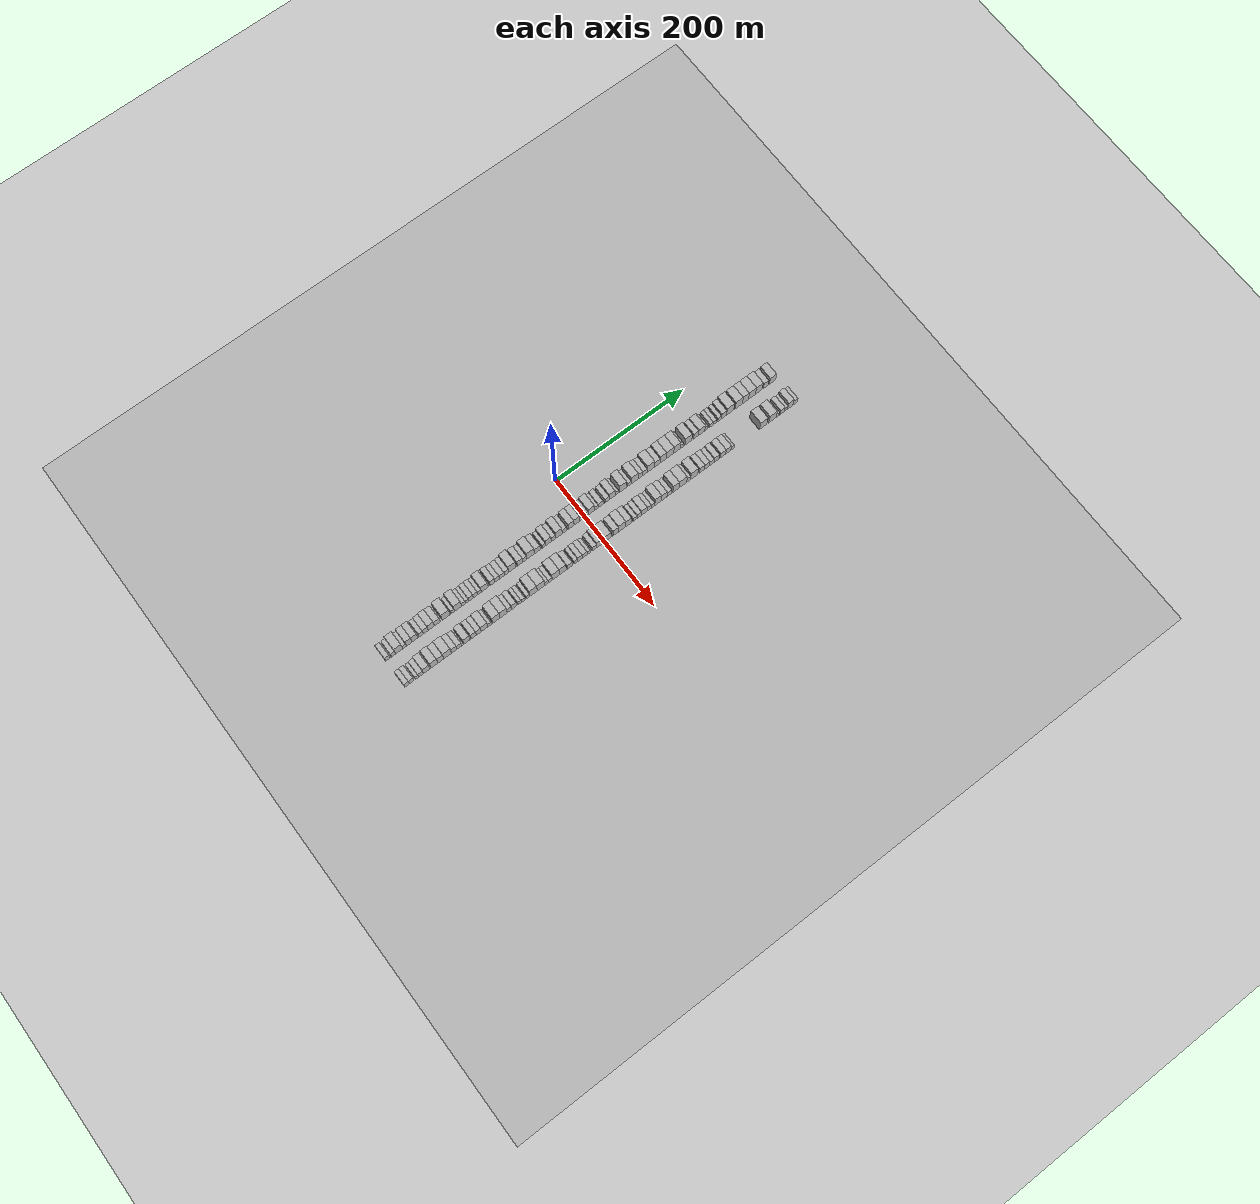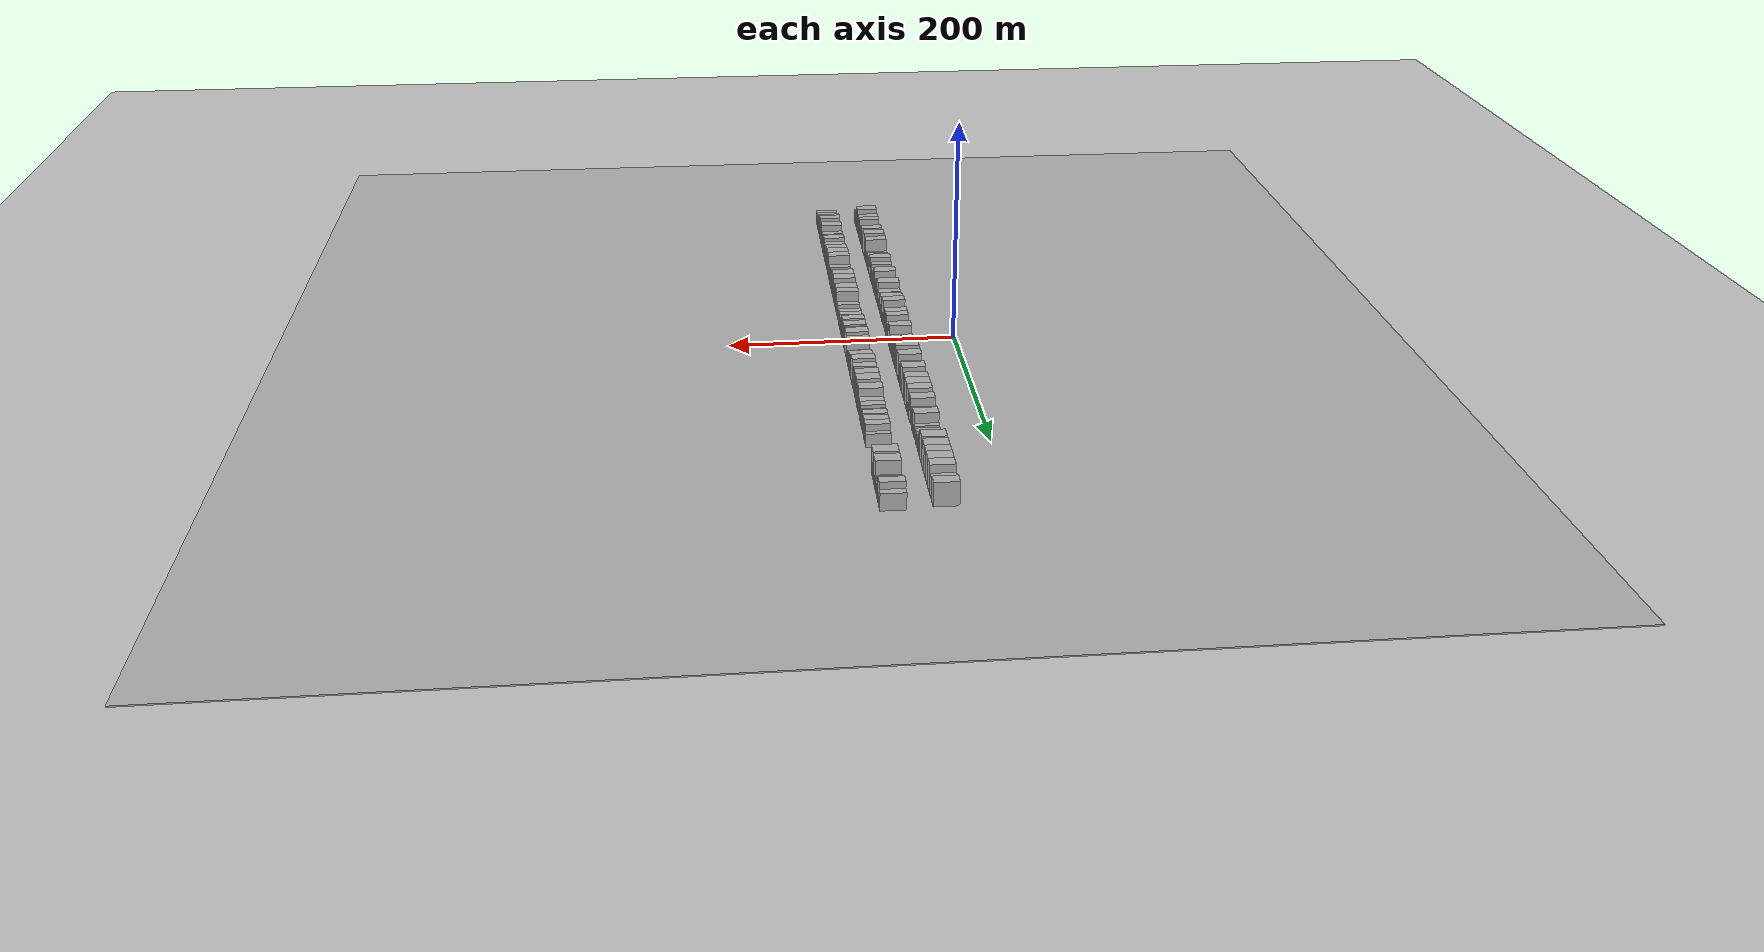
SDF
<?xml version="1.0" encoding="utf-8"?>

<sdf version="1.6">

   <world name="default">

      <gui fullscreen="0">

         <camera name="user_camera">

            <pose>-15 0 4.57585 0 0 0</pose>

            <view_controller>orbit</view_controller>

         </camera>

      </gui>

      <scene>

         <sky>

           <clouds>

             <speed>12</speed>

           </clouds>

         </sky>

         <ambient>0.4 0.4 0.4 1</ambient>

         <background>0.7 0.7 0.7 1</background>

         <shadows>1</shadows>

      </scene>

      <gravity>0 0 -9.8066</gravity>

      <magnetic_field>6e-06 2.3e-05 -4.2e-05</magnetic_field>

      <physics default="0" name="default_physics" type="ode">

         <ode>

            <solver>

               <type>quick</type>

               <iters>10</iters>

               <sor>1.0</sor>

               <use_dynamic_moi_rescaling>0</use_dynamic_moi_rescaling>

            </solver>

            <constraints>

               <cfm>0</cfm>

               <erp>0.2</erp>

               <contact_max_correcting_vel>100</contact_max_correcting_vel>

               <contact_surface_layer>0.001</contact_surface_layer>

            </constraints>

         </ode>

         <max_step_size>0.004</max_step_size>

         <real_time_factor>1</real_time_factor>

         <real_time_update_rate>250</real_time_update_rate>

      </physics>

      <light name="sun" type="directional">

         <cast_shadows>1</cast_shadows>

         <pose>0 0 10 0 0 0</pose>

         <diffuse>0.8 0.8 0.8 1</diffuse>

         <specular>0.2 0.2 0.2 1</specular>

         <attenuation>

            <range>1000</range>

            <constant>0.9</constant>

            <linear>0.01</linear>

            <quadratic>0.001</quadratic>

         </attenuation>

         <direction>-0.5 0.1 -0.9</direction>

      </light>

      <include>

         <name>ground_plane_1</name>

         <uri>model://HANNAS_ground_plane</uri>

         <pose>0 0 0  0 0 0</pose>

      </include>

      <include>

         <name>ground_plane_2</name>

         <uri>model://HANNAS_ground_plane</uri>

         <pose>100 0 0  0 0 0</pose>

      </include>

      <model name="building_1">

         <static>1</static>

         <pose frame="">50.0000 -296.6885 0 0.000000 0.000000 0.000000</pose>

         <link name="link">

            <pose frame="">0 0 7.50 0 0 0</pose>

            <collision name="collision">

               <geometry>

                  <box>

                     <size>20.0000 6.6230 15.0000</size>

                  </box>

               </geometry>

               <max_contacts>10</max_contacts>

               <surface>

                  <contact>

                     <ode/>

                  </contact>

                  <bounce/>

                  <friction>

                     <torsional>

                        <ode/>

                     </torsional>

                     <ode/>

                  </friction>

               </surface>

            </collision>

            <visual name="visual">

               <cast_shadows>0</cast_shadows>

               <geometry>

                  <box>

                     <size>20.0000 6.6230 15.0000</size>

                  </box>

               </geometry>

               <material>

                  <script>

                     <uri>model://HANNAS_wall/materials/scripts</uri>

                     <uri>model://HANNAS_wall/materials/textures</uri>

                     <name>vrc/HANNAS_wall</name>

                  </script>

               </material>

            </visual>

            <self_collide>0</self_collide>

            <enable_wind>0</enable_wind>

            <kinematic>0</kinematic>

         </link>

      </model>

      <model name="building_2">

         <static>1</static>

         <pose frame="">50.0000 -288.3620 0 0.000000 0.000000 0.000000</pose>

         <link name="link">

            <pose frame="">0 0 7.50 0 0 0</pose>

            <collision name="collision">

               <geometry>

                  <box>

                     <size>20.0000 6.0301 15.0000</size>

                  </box>

               </geometry>

               <max_contacts>10</max_contacts>

               <surface>

                  <contact>

                     <ode/>

                  </contact>

                  <bounce/>

                  <friction>

                     <torsional>

                        <ode/>

                     </torsional>

                     <ode/>

                  </friction>

               </surface>

            </collision>

            <visual name="visual">

               <cast_shadows>0</cast_shadows>

               <geometry>

                  <box>

                     <size>20.0000 6.0301 15.0000</size>

                  </box>

               </geometry>

               <material>

                  <script>

                     <uri>model://HANNAS_wall/materials/scripts</uri>

                     <uri>model://HANNAS_wall/materials/textures</uri>

                     <name>vrc/HANNAS_wall</name>

                  </script>

               </material>

            </visual>

            <self_collide>0</self_collide>

            <enable_wind>0</enable_wind>

            <kinematic>0</kinematic>

         </link>

      </model>

      <model name="building_3">

         <static>1</static>

         <pose frame="">50.0000 -280.0617 0 0.000000 0.000000 0.000000</pose>

         <link name="link">

            <pose frame="">0 0 12.00 0 0 0</pose>

            <collision name="collision">

               <geometry>

                  <box>

                     <size>20.0000 10.5706 24.0000</size>

                  </box>

               </geometry>

               <max_contacts>10</max_contacts>

               <surface>

                  <contact>

                     <ode/>

                  </contact>

                  <bounce/>

                  <friction>

                     <torsional>

                        <ode/>

                     </torsional>

                     <ode/>

                  </friction>

               </surface>

            </collision>

            <visual name="visual">

               <cast_shadows>0</cast_shadows>

               <geometry>

                  <box>

                     <size>20.0000 10.5706 24.0000</size>

                  </box>

               </geometry>

               <material>

                  <script>

                     <uri>model://HANNAS_wall/materials/scripts</uri>

                     <uri>model://HANNAS_wall/materials/textures</uri>

                     <name>vrc/HANNAS_wall</name>

                  </script>

               </material>

            </visual>

            <self_collide>0</self_collide>

            <enable_wind>0</enable_wind>

            <kinematic>0</kinematic>

         </link>

      </model>

      <model name="building_4">

         <static>1</static>

         <pose frame="">50.0000 -272.0623 0 0.000000 0.000000 0.000000</pose>

         <link name="link">

            <pose frame="">0 0 6.00 0 0 0</pose>

            <collision name="collision">

               <geometry>

                  <box>

                     <size>20.0000 5.4283 12.0000</size>

                  </box>

               </geometry>

               <max_contacts>10</max_contacts>

               <surface>

                  <contact>

                     <ode/>

                  </contact>

                  <bounce/>

                  <friction>

                     <torsional>

                        <ode/>

                     </torsional>

                     <ode/>

                  </friction>

               </surface>

            </collision>

            <visual name="visual">

               <cast_shadows>0</cast_shadows>

               <geometry>

                  <box>

                     <size>20.0000 5.4283 12.0000</size>

                  </box>

               </geometry>

               <material>

                  <script>

                     <uri>model://HANNAS_wall/materials/scripts</uri>

                     <uri>model://HANNAS_wall/materials/textures</uri>

                     <name>vrc/HANNAS_wall</name>

                  </script>

               </material>

            </visual>

            <self_collide>0</self_collide>

            <enable_wind>0</enable_wind>

            <kinematic>0</kinematic>

         </link>

      </model>

      <model name="building_5">

         <static>1</static>

         <pose frame="">50.0000 -265.1304 0 0.000000 0.000000 0.000000</pose>

         <link name="link">

            <pose frame="">0 0 10.50 0 0 0</pose>

            <collision name="collision">

               <geometry>

                  <box>

                     <size>20.0000 8.4354 21.0000</size>

                  </box>

               </geometry>

               <max_contacts>10</max_contacts>

               <surface>

                  <contact>

                     <ode/>

                  </contact>

                  <bounce/>

                  <friction>

                     <torsional>

                        <ode/>

                     </torsional>

                     <ode/>

                  </friction>

               </surface>

            </collision>

            <visual name="visual">

               <cast_shadows>0</cast_shadows>

               <geometry>

                  <box>

                     <size>20.0000 8.4354 21.0000</size>

                  </box>

               </geometry>

               <material>

                  <script>

                     <uri>model://HANNAS_wall/materials/scripts</uri>

                     <uri>model://HANNAS_wall/materials/textures</uri>

                     <name>vrc/HANNAS_wall</name>

                  </script>

               </material>

            </visual>

            <self_collide>0</self_collide>

            <enable_wind>0</enable_wind>

            <kinematic>0</kinematic>

         </link>

      </model>

      <model name="building_6">

         <static>1</static>

         <pose frame="">50.0000 -256.7108 0 0.000000 0.000000 0.000000</pose>

         <link name="link">

            <pose frame="">0 0 10.50 0 0 0</pose>

            <collision name="collision">

               <geometry>

                  <box>

                     <size>20.0000 8.4038 21.0000</size>

                  </box>

               </geometry>

               <max_contacts>10</max_contacts>

               <surface>

                  <contact>

                     <ode/>

                  </contact>

                  <bounce/>

                  <friction>

                     <torsional>

                        <ode/>

                     </torsional>

                     <ode/>

                  </friction>

               </surface>

            </collision>

            <visual name="visual">

               <cast_shadows>0</cast_shadows>

               <geometry>

                  <box>

                     <size>20.0000 8.4038 21.0000</size>

                  </box>

               </geometry>

               <material>

                  <script>

                     <uri>model://HANNAS_wall/materials/scripts</uri>

                     <uri>model://HANNAS_wall/materials/textures</uri>

                     <name>vrc/HANNAS_wall</name>

                  </script>

               </material>

            </visual>

            <self_collide>0</self_collide>

            <enable_wind>0</enable_wind>

            <kinematic>0</kinematic>

         </link>

      </model>

      <model name="building_7">

         <static>1</static>

         <pose frame="">50.0000 -247.4542 0 0.000000 0.000000 0.000000</pose>

         <link name="link">

            <pose frame="">0 0 7.50 0 0 0</pose>

            <collision name="collision">

               <geometry>

                  <box>

                     <size>20.0000 6.1095 15.0000</size>

                  </box>

               </geometry>

               <max_contacts>10</max_contacts>

               <surface>

                  <contact>

                     <ode/>

                  </contact>

                  <bounce/>

                  <friction>

                     <torsional>

                        <ode/>

                     </torsional>

                     <ode/>

                  </friction>

               </surface>

            </collision>

            <visual name="visual">

               <cast_shadows>0</cast_shadows>

               <geometry>

                  <box>

                     <size>20.0000 6.1095 15.0000</size>

                  </box>

               </geometry>

               <material>

                  <script>

                     <uri>model://HANNAS_wall/materials/scripts</uri>

                     <uri>model://HANNAS_wall/materials/textures</uri>

                     <name>vrc/HANNAS_wall</name>

                  </script>

               </material>

            </visual>

            <self_collide>0</self_collide>

            <enable_wind>0</enable_wind>

            <kinematic>0</kinematic>

         </link>

      </model>

      <model name="building_8">

         <static>1</static>

         <pose frame="">50.0000 -240.6647 0 0.000000 0.000000 0.000000</pose>

         <link name="link">

            <pose frame="">0 0 9.00 0 0 0</pose>

            <collision name="collision">

               <geometry>

                  <box>

                     <size>20.0000 7.4693 18.0000</size>

                  </box>

               </geometry>

               <max_contacts>10</max_contacts>

               <surface>

                  <contact>

                     <ode/>

                  </contact>

                  <bounce/>

                  <friction>

                     <torsional>

                        <ode/>

                     </torsional>

                     <ode/>

                  </friction>

               </surface>

            </collision>

            <visual name="visual">

               <cast_shadows>0</cast_shadows>

               <geometry>

                  <box>

                     <size>20.0000 7.4693 18.0000</size>

                  </box>

               </geometry>

               <material>

                  <script>

                     <uri>model://HANNAS_wall/materials/scripts</uri>

                     <uri>model://HANNAS_wall/materials/textures</uri>

                     <name>vrc/HANNAS_wall</name>

                  </script>

               </material>

            </visual>

            <self_collide>0</self_collide>

            <enable_wind>0</enable_wind>

            <kinematic>0</kinematic>

         </link>

      </model>

      <model name="building_9">

         <static>1</static>

         <pose frame="">50.0000 -232.4220 0 0.000000 0.000000 0.000000</pose>

         <link name="link">

            <pose frame="">0 0 10.50 0 0 0</pose>

            <collision name="collision">

               <geometry>

                  <box>

                     <size>20.0000 9.0161 21.0000</size>

                  </box>

               </geometry>

               <max_contacts>10</max_contacts>

               <surface>

                  <contact>

                     <ode/>

                  </contact>

                  <bounce/>

                  <friction>

                     <torsional>

                        <ode/>

                     </torsional>

                     <ode/>

                  </friction>

               </surface>

            </collision>

            <visual name="visual">

               <cast_shadows>0</cast_shadows>

               <geometry>

                  <box>

                     <size>20.0000 9.0161 21.0000</size>

                  </box>

               </geometry>

               <material>

                  <script>

                     <uri>model://HANNAS_wall/materials/scripts</uri>

                     <uri>model://HANNAS_wall/materials/textures</uri>

                     <name>vrc/HANNAS_wall</name>

                  </script>

               </material>

            </visual>

            <self_collide>0</self_collide>

            <enable_wind>0</enable_wind>

            <kinematic>0</kinematic>

         </link>

      </model>

      <model name="building_10">

         <static>1</static>

         <pose frame="">50.0000 -223.6112 0 0.000000 0.000000 0.000000</pose>

         <link name="link">

            <pose frame="">0 0 9.00 0 0 0</pose>

            <collision name="collision">

               <geometry>

                  <box>

                     <size>20.0000 8.6056 18.0000</size>

                  </box>

               </geometry>

               <max_contacts>10</max_contacts>

               <surface>

                  <contact>

                     <ode/>

                  </contact>

                  <bounce/>

                  <friction>

                     <torsional>

                        <ode/>

                     </torsional>

                     <ode/>

                  </friction>

               </surface>

            </collision>

            <visual name="visual">

               <cast_shadows>0</cast_shadows>

               <geometry>

                  <box>

                     <size>20.0000 8.6056 18.0000</size>

                  </box>

               </geometry>

               <material>

                  <script>

                     <uri>model://HANNAS_wall/materials/scripts</uri>

                     <uri>model://HANNAS_wall/materials/textures</uri>

                     <name>vrc/HANNAS_wall</name>

                  </script>

               </material>

            </visual>

            <self_collide>0</self_collide>

            <enable_wind>0</enable_wind>

            <kinematic>0</kinematic>

         </link>

      </model>

      <model name="building_11">

         <static>1</static>

         <pose frame="">50.0000 -210.5880 0 0.000000 0.000000 0.000000</pose>

         <link name="link">

            <pose frame="">0 0 12.00 0 0 0</pose>

            <collision name="collision">

               <geometry>

                  <box>

                     <size>20.0000 11.4408 24.0000</size>

                  </box>

               </geometry>

               <max_contacts>10</max_contacts>

               <surface>

                  <contact>

                     <ode/>

                  </contact>

                  <bounce/>

                  <friction>

                     <torsional>

                        <ode/>

                     </torsional>

                     <ode/>

                  </friction>

               </surface>

            </collision>

            <visual name="visual">

               <cast_shadows>0</cast_shadows>

               <geometry>

                  <box>

                     <size>20.0000 11.4408 24.0000</size>

                  </box>

               </geometry>

               <material>

                  <script>

                     <uri>model://HANNAS_wall/materials/scripts</uri>

                     <uri>model://HANNAS_wall/materials/textures</uri>

                     <name>vrc/HANNAS_wall</name>

                  </script>

               </material>

            </visual>

            <self_collide>0</self_collide>

            <enable_wind>0</enable_wind>

            <kinematic>0</kinematic>

         </link>

      </model>

      <model name="building_12">

         <static>1</static>

         <pose frame="">50.0000 -200.3734 0 0.000000 0.000000 0.000000</pose>

         <link name="link">

            <pose frame="">0 0 6.00 0 0 0</pose>

            <collision name="collision">

               <geometry>

                  <box>

                     <size>20.0000 4.9884 12.0000</size>

                  </box>

               </geometry>

               <max_contacts>10</max_contacts>

               <surface>

                  <contact>

                     <ode/>

                  </contact>

                  <bounce/>

                  <friction>

                     <torsional>

                        <ode/>

                     </torsional>

                     <ode/>

                  </friction>

               </surface>

            </collision>

            <visual name="visual">

               <cast_shadows>0</cast_shadows>

               <geometry>

                  <box>

                     <size>20.0000 4.9884 12.0000</size>

                  </box>

               </geometry>

               <material>

                  <script>

                     <uri>model://HANNAS_wall/materials/scripts</uri>

                     <uri>model://HANNAS_wall/materials/textures</uri>

                     <name>vrc/HANNAS_wall</name>

                  </script>

               </material>

            </visual>

            <self_collide>0</self_collide>

            <enable_wind>0</enable_wind>

            <kinematic>0</kinematic>

         </link>

      </model>

      <model name="building_13">

         <static>1</static>

         <pose frame="">50.0000 -192.5975 0 0.000000 0.000000 0.000000</pose>

         <link name="link">

            <pose frame="">0 0 12.00 0 0 0</pose>

            <collision name="collision">

               <geometry>

                  <box>

                     <size>20.0000 10.5634 24.0000</size>

                  </box>

               </geometry>

               <max_contacts>10</max_contacts>

               <surface>

                  <contact>

                     <ode/>

                  </contact>

                  <bounce/>

                  <friction>

                     <torsional>

                        <ode/>

                     </torsional>

                     <ode/>

                  </friction>

               </surface>

            </collision>

            <visual name="visual">

               <cast_shadows>0</cast_shadows>

               <geometry>

                  <box>

                     <size>20.0000 10.5634 24.0000</size>

                  </box>

               </geometry>

               <material>

                  <script>

                     <uri>model://HANNAS_wall/materials/scripts</uri>

                     <uri>model://HANNAS_wall/materials/textures</uri>

                     <name>vrc/HANNAS_wall</name>

                  </script>

               </material>

            </visual>

            <self_collide>0</self_collide>

            <enable_wind>0</enable_wind>

            <kinematic>0</kinematic>

         </link>

      </model>

      <model name="building_14">

         <static>1</static>

         <pose frame="">50.0000 -184.3863 0 0.000000 0.000000 0.000000</pose>

         <link name="link">

            <pose frame="">0 0 6.00 0 0 0</pose>

            <collision name="collision">

               <geometry>

                  <box>

                     <size>20.0000 5.8589 12.0000</size>

                  </box>

               </geometry>

               <max_contacts>10</max_contacts>

               <surface>

                  <contact>

                     <ode/>

                  </contact>

                  <bounce/>

                  <friction>

                     <torsional>

                        <ode/>

                     </torsional>

                     <ode/>

                  </friction>

               </surface>

            </collision>

            <visual name="visual">

               <cast_shadows>0</cast_shadows>

               <geometry>

                  <box>

                     <size>20.0000 5.8589 12.0000</size>

                  </box>

               </geometry>

               <material>

                  <script>

                     <uri>model://HANNAS_wall/materials/scripts</uri>

                     <uri>model://HANNAS_wall/materials/textures</uri>

                     <name>vrc/HANNAS_wall</name>

                  </script>

               </material>

            </visual>

            <self_collide>0</self_collide>

            <enable_wind>0</enable_wind>

            <kinematic>0</kinematic>

         </link>

      </model>

      <model name="building_15">

         <static>1</static>

         <pose frame="">50.0000 -179.0469 0 0.000000 0.000000 0.000000</pose>

         <link name="link">

            <pose frame="">0 0 6.00 0 0 0</pose>

            <collision name="collision">

               <geometry>

                  <box>

                     <size>20.0000 4.8199 12.0000</size>

                  </box>

               </geometry>

               <max_contacts>10</max_contacts>

               <surface>

                  <contact>

                     <ode/>

                  </contact>

                  <bounce/>

                  <friction>

                     <torsional>

                        <ode/>

                     </torsional>

                     <ode/>

                  </friction>

               </surface>

            </collision>

            <visual name="visual">

               <cast_shadows>0</cast_shadows>

               <geometry>

                  <box>

                     <size>20.0000 4.8199 12.0000</size>

                  </box>

               </geometry>

               <material>

                  <script>

                     <uri>model://HANNAS_wall/materials/scripts</uri>

                     <uri>model://HANNAS_wall/materials/textures</uri>

                     <name>vrc/HANNAS_wall</name>

                  </script>

               </material>

            </visual>

            <self_collide>0</self_collide>

            <enable_wind>0</enable_wind>

            <kinematic>0</kinematic>

         </link>

      </model>

      <model name="building_16">

         <static>1</static>

         <pose frame="">50.0000 -173.2022 0 0.000000 0.000000 0.000000</pose>

         <link name="link">

            <pose frame="">0 0 7.50 0 0 0</pose>

            <collision name="collision">

               <geometry>

                  <box>

                     <size>20.0000 6.8695 15.0000</size>

                  </box>

               </geometry>

               <max_contacts>10</max_contacts>

               <surface>

                  <contact>

                     <ode/>

                  </contact>

                  <bounce/>

                  <friction>

                     <torsional>

                        <ode/>

                     </torsional>

                     <ode/>

                  </friction>

               </surface>

            </collision>

            <visual name="visual">

               <cast_shadows>0</cast_shadows>

               <geometry>

                  <box>

                     <size>20.0000 6.8695 15.0000</size>

                  </box>

               </geometry>

               <material>

                  <script>

                     <uri>model://HANNAS_wall/materials/scripts</uri>

                     <uri>model://HANNAS_wall/materials/textures</uri>

                     <name>vrc/HANNAS_wall</name>

                  </script>

               </material>

            </visual>

            <self_collide>0</self_collide>

            <enable_wind>0</enable_wind>

            <kinematic>0</kinematic>

         </link>

      </model>

      <model name="building_17">

         <static>1</static>

         <pose frame="">50.0000 -166.3987 0 0.000000 0.000000 0.000000</pose>

         <link name="link">

            <pose frame="">0 0 7.50 0 0 0</pose>

            <collision name="collision">

               <geometry>

                  <box>

                     <size>20.0000 6.7375 15.0000</size>

                  </box>

               </geometry>

               <max_contacts>10</max_contacts>

               <surface>

                  <contact>

                     <ode/>

                  </contact>

                  <bounce/>

                  <friction>

                     <torsional>

                        <ode/>

                     </torsional>

                     <ode/>

                  </friction>

               </surface>

            </collision>

            <visual name="visual">

               <cast_shadows>0</cast_shadows>

               <geometry>

                  <box>

                     <size>20.0000 6.7375 15.0000</size>

                  </box>

               </geometry>

               <material>

                  <script>

                     <uri>model://HANNAS_wall/materials/scripts</uri>

                     <uri>model://HANNAS_wall/materials/textures</uri>

                     <name>vrc/HANNAS_wall</name>

                  </script>

               </material>

            </visual>

            <self_collide>0</self_collide>

            <enable_wind>0</enable_wind>

            <kinematic>0</kinematic>

         </link>

      </model>

      <model name="building_18">

         <static>1</static>

         <pose frame="">50.0000 -160.3382 0 0.000000 0.000000 0.000000</pose>

         <link name="link">

            <pose frame="">0 0 6.00 0 0 0</pose>

            <collision name="collision">

               <geometry>

                  <box>

                     <size>20.0000 5.3836 12.0000</size>

                  </box>

               </geometry>

               <max_contacts>10</max_contacts>

               <surface>

                  <contact>

                     <ode/>

                  </contact>

                  <bounce/>

                  <friction>

                     <torsional>

                        <ode/>

                     </torsional>

                     <ode/>

                  </friction>

               </surface>

            </collision>

            <visual name="visual">

               <cast_shadows>0</cast_shadows>

               <geometry>

                  <box>

                     <size>20.0000 5.3836 12.0000</size>

                  </box>

               </geometry>

               <material>

                  <script>

                     <uri>model://HANNAS_wall/materials/scripts</uri>

                     <uri>model://HANNAS_wall/materials/textures</uri>

                     <name>vrc/HANNAS_wall</name>

                  </script>

               </material>

            </visual>

            <self_collide>0</self_collide>

            <enable_wind>0</enable_wind>

            <kinematic>0</kinematic>

         </link>

      </model>

      <model name="building_19">

         <static>1</static>

         <pose frame="">50.0000 -152.5379 0 0.000000 0.000000 0.000000</pose>

         <link name="link">

            <pose frame="">0 0 10.50 0 0 0</pose>

            <collision name="collision">

               <geometry>

                  <box>

                     <size>20.0000 10.2169 21.0000</size>

                  </box>

               </geometry>

               <max_contacts>10</max_contacts>

               <surface>

                  <contact>

                     <ode/>

                  </contact>

                  <bounce/>

                  <friction>

                     <torsional>

                        <ode/>

                     </torsional>

                     <ode/>

                  </friction>

               </surface>

            </collision>

            <visual name="visual">

               <cast_shadows>0</cast_shadows>

               <geometry>

                  <box>

                     <size>20.0000 10.2169 21.0000</size>

                  </box>

               </geometry>

               <material>

                  <script>

                     <uri>model://HANNAS_wall/materials/scripts</uri>

                     <uri>model://HANNAS_wall/materials/textures</uri>

                     <name>vrc/HANNAS_wall</name>

                  </script>

               </material>

            </visual>

            <self_collide>0</self_collide>

            <enable_wind>0</enable_wind>

            <kinematic>0</kinematic>

         </link>

      </model>

      <model name="building_20">

         <static>1</static>

         <pose frame="">50.0000 -140.7520 0 0.000000 0.000000 0.000000</pose>

         <link name="link">

            <pose frame="">0 0 9.00 0 0 0</pose>

            <collision name="collision">

               <geometry>

                  <box>

                     <size>20.0000 7.3550 18.0000</size>

                  </box>

               </geometry>

               <max_contacts>10</max_contacts>

               <surface>

                  <contact>

                     <ode/>

                  </contact>

                  <bounce/>

                  <friction>

                     <torsional>

                        <ode/>

                     </torsional>

                     <ode/>

                  </friction>

               </surface>

            </collision>

            <visual name="visual">

               <cast_shadows>0</cast_shadows>

               <geometry>

                  <box>

                     <size>20.0000 7.3550 18.0000</size>

                  </box>

               </geometry>

               <material>

                  <script>

                     <uri>model://HANNAS_wall/materials/scripts</uri>

                     <uri>model://HANNAS_wall/materials/textures</uri>

                     <name>vrc/HANNAS_wall</name>

                  </script>

               </material>

            </visual>

            <self_collide>0</self_collide>

            <enable_wind>0</enable_wind>

            <kinematic>0</kinematic>

         </link>

      </model>

      <model name="building_21">

         <static>1</static>

         <pose frame="">50.0000 -133.7475 0 0.000000 0.000000 0.000000</pose>

         <link name="link">

            <pose frame="">0 0 7.50 0 0 0</pose>

            <collision name="collision">

               <geometry>

                  <box>

                     <size>20.0000 6.6540 15.0000</size>

                  </box>

               </geometry>

               <max_contacts>10</max_contacts>

               <surface>

                  <contact>

                     <ode/>

                  </contact>

                  <bounce/>

                  <friction>

                     <torsional>

                        <ode/>

                     </torsional>

                     <ode/>

                  </friction>

               </surface>

            </collision>

            <visual name="visual">

               <cast_shadows>0</cast_shadows>

               <geometry>

                  <box>

                     <size>20.0000 6.6540 15.0000</size>

                  </box>

               </geometry>

               <material>

                  <script>

                     <uri>model://HANNAS_wall/materials/scripts</uri>

                     <uri>model://HANNAS_wall/materials/textures</uri>

                     <name>vrc/HANNAS_wall</name>

                  </script>

               </material>

            </visual>

            <self_collide>0</self_collide>

            <enable_wind>0</enable_wind>

            <kinematic>0</kinematic>

         </link>

      </model>

      <model name="building_22">

         <static>1</static>

         <pose frame="">50.0000 -126.6959 0 0.000000 0.000000 0.000000</pose>

         <link name="link">

            <pose frame="">0 0 7.50 0 0 0</pose>

            <collision name="collision">

               <geometry>

                  <box>

                     <size>20.0000 7.4490 15.0000</size>

                  </box>

               </geometry>

               <max_contacts>10</max_contacts>

               <surface>

                  <contact>

                     <ode/>

                  </contact>

                  <bounce/>

                  <friction>

                     <torsional>

                        <ode/>

                     </torsional>

                     <ode/>

                  </friction>

               </surface>

            </collision>

            <visual name="visual">

               <cast_shadows>0</cast_shadows>

               <geometry>

                  <box>

                     <size>20.0000 7.4490 15.0000</size>

                  </box>

               </geometry>

               <material>

                  <script>

                     <uri>model://HANNAS_wall/materials/scripts</uri>

                     <uri>model://HANNAS_wall/materials/textures</uri>

                     <name>vrc/HANNAS_wall</name>

                  </script>

               </material>

            </visual>

            <self_collide>0</self_collide>

            <enable_wind>0</enable_wind>

            <kinematic>0</kinematic>

         </link>

      </model>

      <model name="building_23">

         <static>1</static>

         <pose frame="">50.0000 -119.7036 0 0.000000 0.000000 0.000000</pose>

         <link name="link">

            <pose frame="">0 0 7.50 0 0 0</pose>

            <collision name="collision">

               <geometry>

                  <box>

                     <size>20.0000 6.5356 15.0000</size>

                  </box>

               </geometry>

               <max_contacts>10</max_contacts>

               <surface>

                  <contact>

                     <ode/>

                  </contact>

                  <bounce/>

                  <friction>

                     <torsional>

                        <ode/>

                     </torsional>

                     <ode/>

                  </friction>

               </surface>

            </collision>

            <visual name="visual">

               <cast_shadows>0</cast_shadows>

               <geometry>

                  <box>

                     <size>20.0000 6.5356 15.0000</size>

                  </box>

               </geometry>

               <material>

                  <script>

                     <uri>model://HANNAS_wall/materials/scripts</uri>

                     <uri>model://HANNAS_wall/materials/textures</uri>

                     <name>vrc/HANNAS_wall</name>

                  </script>

               </material>

            </visual>

            <self_collide>0</self_collide>

            <enable_wind>0</enable_wind>

            <kinematic>0</kinematic>

         </link>

      </model>

      <model name="building_24">

         <static>1</static>

         <pose frame="">50.0000 -110.8735 0 0.000000 0.000000 0.000000</pose>

         <link name="link">

            <pose frame="">0 0 12.00 0 0 0</pose>

            <collision name="collision">

               <geometry>

                  <box>

                     <size>20.0000 11.1247 24.0000</size>

                  </box>

               </geometry>

               <max_contacts>10</max_contacts>

               <surface>

                  <contact>

                     <ode/>

                  </contact>

                  <bounce/>

                  <friction>

                     <torsional>

                        <ode/>

                     </torsional>

                     <ode/>

                  </friction>

               </surface>

            </collision>

            <visual name="visual">

               <cast_shadows>0</cast_shadows>

               <geometry>

                  <box>

                     <size>20.0000 11.1247 24.0000</size>

                  </box>

               </geometry>

               <material>

                  <script>

                     <uri>model://HANNAS_wall/materials/scripts</uri>

                     <uri>model://HANNAS_wall/materials/textures</uri>

                     <name>vrc/HANNAS_wall</name>

                  </script>

               </material>

            </visual>

            <self_collide>0</self_collide>

            <enable_wind>0</enable_wind>

            <kinematic>0</kinematic>

         </link>

      </model>

      <model name="building_25">

         <static>1</static>

         <pose frame="">50.0000 -99.2027 0 0.000000 0.000000 0.000000</pose>

         <link name="link">

            <pose frame="">0 0 9.00 0 0 0</pose>

            <collision name="collision">

               <geometry>

                  <box>

                     <size>20.0000 8.2169 18.0000</size>

                  </box>

               </geometry>

               <max_contacts>10</max_contacts>

               <surface>

                  <contact>

                     <ode/>

                  </contact>

                  <bounce/>

                  <friction>

                     <torsional>

                        <ode/>

                     </torsional>

                     <ode/>

                  </friction>

               </surface>

            </collision>

            <visual name="visual">

               <cast_shadows>0</cast_shadows>

               <geometry>

                  <box>

                     <size>20.0000 8.2169 18.0000</size>

                  </box>

               </geometry>

               <material>

                  <script>

                     <uri>model://HANNAS_wall/materials/scripts</uri>

                     <uri>model://HANNAS_wall/materials/textures</uri>

                     <name>vrc/HANNAS_wall</name>

                  </script>

               </material>

            </visual>

            <self_collide>0</self_collide>

            <enable_wind>0</enable_wind>

            <kinematic>0</kinematic>

         </link>

      </model>

      <model name="building_26">

         <static>1</static>

         <pose frame="">50.0000 -91.9882 0 0.000000 0.000000 0.000000</pose>

         <link name="link">

            <pose frame="">0 0 7.50 0 0 0</pose>

            <collision name="collision">

               <geometry>

                  <box>

                     <size>20.0000 6.2121 15.0000</size>

                  </box>

               </geometry>

               <max_contacts>10</max_contacts>

               <surface>

                  <contact>

                     <ode/>

                  </contact>

                  <bounce/>

                  <friction>

                     <torsional>

                        <ode/>

                     </torsional>

                     <ode/>

                  </friction>

               </surface>

            </collision>

            <visual name="visual">

               <cast_shadows>0</cast_shadows>

               <geometry>

                  <box>

                     <size>20.0000 6.2121 15.0000</size>

                  </box>

               </geometry>

               <material>

                  <script>

                     <uri>model://HANNAS_wall/materials/scripts</uri>

                     <uri>model://HANNAS_wall/materials/textures</uri>

                     <name>vrc/HANNAS_wall</name>

                  </script>

               </material>

            </visual>

            <self_collide>0</self_collide>

            <enable_wind>0</enable_wind>

            <kinematic>0</kinematic>

         </link>

      </model>

      <model name="building_27">

         <static>1</static>

         <pose frame="">50.0000 -83.1758 0 0.000000 0.000000 0.000000</pose>

         <link name="link">

            <pose frame="">0 0 12.00 0 0 0</pose>

            <collision name="collision">

               <geometry>

                  <box>

                     <size>20.0000 11.4127 24.0000</size>

                  </box>

               </geometry>

               <max_contacts>10</max_contacts>

               <surface>

                  <contact>

                     <ode/>

                  </contact>

                  <bounce/>

                  <friction>

                     <torsional>

                        <ode/>

                     </torsional>

                     <ode/>

                  </friction>

               </surface>

            </collision>

            <visual name="visual">

               <cast_shadows>0</cast_shadows>

               <geometry>

                  <box>

                     <size>20.0000 11.4127 24.0000</size>

                  </box>

               </geometry>

               <material>

                  <script>

                     <uri>model://HANNAS_wall/materials/scripts</uri>

                     <uri>model://HANNAS_wall/materials/textures</uri>

                     <name>vrc/HANNAS_wall</name>

                  </script>

               </material>

            </visual>

            <self_collide>0</self_collide>

            <enable_wind>0</enable_wind>

            <kinematic>0</kinematic>

         </link>

      </model>

      <model name="building_28">

         <static>1</static>

         <pose frame="">50.0000 -72.9829 0 0.000000 0.000000 0.000000</pose>

         <link name="link">

            <pose frame="">0 0 9.00 0 0 0</pose>

            <collision name="collision">

               <geometry>

                  <box>

                     <size>20.0000 8.9731 18.0000</size>

                  </box>

               </geometry>

               <max_contacts>10</max_contacts>

               <surface>

                  <contact>

                     <ode/>

                  </contact>

                  <bounce/>

                  <friction>

                     <torsional>

                        <ode/>

                     </torsional>

                     <ode/>

                  </friction>

               </surface>

            </collision>

            <visual name="visual">

               <cast_shadows>0</cast_shadows>

               <geometry>

                  <box>

                     <size>20.0000 8.9731 18.0000</size>

                  </box>

               </geometry>

               <material>

                  <script>

                     <uri>model://HANNAS_wall/materials/scripts</uri>

                     <uri>model://HANNAS_wall/materials/textures</uri>

                     <name>vrc/HANNAS_wall</name>

                  </script>

               </material>

            </visual>

            <self_collide>0</self_collide>

            <enable_wind>0</enable_wind>

            <kinematic>0</kinematic>

         </link>

      </model>

      <model name="building_29">

         <static>1</static>

         <pose frame="">50.0000 -63.0117 0 0.000000 0.000000 0.000000</pose>

         <link name="link">

            <pose frame="">0 0 6.00 0 0 0</pose>

            <collision name="collision">

               <geometry>

                  <box>

                     <size>20.0000 4.9692 12.0000</size>

                  </box>

               </geometry>

               <max_contacts>10</max_contacts>

               <surface>

                  <contact>

                     <ode/>

                  </contact>

                  <bounce/>

                  <friction>

                     <torsional>

                        <ode/>

                     </torsional>

                     <ode/>

                  </friction>

               </surface>

            </collision>

            <visual name="visual">

               <cast_shadows>0</cast_shadows>

               <geometry>

                  <box>

                     <size>20.0000 4.9692 12.0000</size>

                  </box>

               </geometry>

               <material>

                  <script>

                     <uri>model://HANNAS_wall/materials/scripts</uri>

                     <uri>model://HANNAS_wall/materials/textures</uri>

                     <name>vrc/HANNAS_wall</name>

                  </script>

               </material>

            </visual>

            <self_collide>0</self_collide>

            <enable_wind>0</enable_wind>

            <kinematic>0</kinematic>

         </link>

      </model>

      <model name="building_30">

         <static>1</static>

         <pose frame="">50.0000 -56.1043 0 0.000000 0.000000 0.000000</pose>

         <link name="link">

            <pose frame="">0 0 10.50 0 0 0</pose>

            <collision name="collision">

               <geometry>

                  <box>

                     <size>20.0000 8.8454 21.0000</size>

                  </box>

               </geometry>

               <max_contacts>10</max_contacts>

               <surface>

                  <contact>

                     <ode/>

                  </contact>

                  <bounce/>

                  <friction>

                     <torsional>

                        <ode/>

                     </torsional>

                     <ode/>

                  </friction>

               </surface>

            </collision>

            <visual name="visual">

               <cast_shadows>0</cast_shadows>

               <geometry>

                  <box>

                     <size>20.0000 8.8454 21.0000</size>

                  </box>

               </geometry>

               <material>

                  <script>

                     <uri>model://HANNAS_wall/materials/scripts</uri>

                     <uri>model://HANNAS_wall/materials/textures</uri>

                     <name>vrc/HANNAS_wall</name>

                  </script>

               </material>

            </visual>

            <self_collide>0</self_collide>

            <enable_wind>0</enable_wind>

            <kinematic>0</kinematic>

         </link>

      </model>

      <model name="building_31">

         <static>1</static>

         <pose frame="">50.0000 -48.2163 0 0.000000 0.000000 0.000000</pose>

         <link name="link">

            <pose frame="">0 0 7.50 0 0 0</pose>

            <collision name="collision">

               <geometry>

                  <box>

                     <size>20.0000 6.9306 15.0000</size>

                  </box>

               </geometry>

               <max_contacts>10</max_contacts>

               <surface>

                  <contact>

                     <ode/>

                  </contact>

                  <bounce/>

                  <friction>

                     <torsional>

                        <ode/>

                     </torsional>

                     <ode/>

                  </friction>

               </surface>

            </collision>

            <visual name="visual">

               <cast_shadows>0</cast_shadows>

               <geometry>

                  <box>

                     <size>20.0000 6.9306 15.0000</size>

                  </box>

               </geometry>

               <material>

                  <script>

                     <uri>model://HANNAS_wall/materials/scripts</uri>

                     <uri>model://HANNAS_wall/materials/textures</uri>

                     <name>vrc/HANNAS_wall</name>

                  </script>

               </material>

            </visual>

            <self_collide>0</self_collide>

            <enable_wind>0</enable_wind>

            <kinematic>0</kinematic>

         </link>

      </model>

      <model name="building_32">

         <static>1</static>

         <pose frame="">50.0000 -39.8728 0 0.000000 0.000000 0.000000</pose>

         <link name="link">

            <pose frame="">0 0 12.00 0 0 0</pose>

            <collision name="collision">

               <geometry>

                  <box>

                     <size>20.0000 9.7566 24.0000</size>

                  </box>

               </geometry>

               <max_contacts>10</max_contacts>

               <surface>

                  <contact>

                     <ode/>

                  </contact>

                  <bounce/>

                  <friction>

                     <torsional>

                        <ode/>

                     </torsional>

                     <ode/>

                  </friction>

               </surface>

            </collision>

            <visual name="visual">

               <cast_shadows>0</cast_shadows>

               <geometry>

                  <box>

                     <size>20.0000 9.7566 24.0000</size>

                  </box>

               </geometry>

               <material>

                  <script>

                     <uri>model://HANNAS_wall/materials/scripts</uri>

                     <uri>model://HANNAS_wall/materials/textures</uri>

                     <name>vrc/HANNAS_wall</name>

                  </script>

               </material>

            </visual>

            <self_collide>0</self_collide>

            <enable_wind>0</enable_wind>

            <kinematic>0</kinematic>

         </link>

      </model>

      <model name="building_33">

         <static>1</static>

         <pose frame="">50.0000 -31.3710 0 0.000000 0.000000 0.000000</pose>

         <link name="link">

            <pose frame="">0 0 7.50 0 0 0</pose>

            <collision name="collision">

               <geometry>

                  <box>

                     <size>20.0000 7.2471 15.0000</size>

                  </box>

               </geometry>

               <max_contacts>10</max_contacts>

               <surface>

                  <contact>

                     <ode/>

                  </contact>

                  <bounce/>

                  <friction>

                     <torsional>

                        <ode/>

                     </torsional>

                     <ode/>

                  </friction>

               </surface>

            </collision>

            <visual name="visual">

               <cast_shadows>0</cast_shadows>

               <geometry>

                  <box>

                     <size>20.0000 7.2471 15.0000</size>

                  </box>

               </geometry>

               <material>

                  <script>

                     <uri>model://HANNAS_wall/materials/scripts</uri>

                     <uri>model://HANNAS_wall/materials/textures</uri>

                     <name>vrc/HANNAS_wall</name>

                  </script>

               </material>

            </visual>

            <self_collide>0</self_collide>

            <enable_wind>0</enable_wind>

            <kinematic>0</kinematic>

         </link>

      </model>

      <model name="building_34">

         <static>1</static>

         <pose frame="">50.0000 -21.2676 0 0.000000 0.000000 0.000000</pose>

         <link name="link">

            <pose frame="">0 0 10.50 0 0 0</pose>

            <collision name="collision">

               <geometry>

                  <box>

                     <size>20.0000 8.9597 21.0000</size>

                  </box>

               </geometry>

               <max_contacts>10</max_contacts>

               <surface>

                  <contact>

                     <ode/>

                  </contact>

                  <bounce/>

                  <friction>

                     <torsional>

                        <ode/>

                     </torsional>

                     <ode/>

                  </friction>

               </surface>

            </collision>

            <visual name="visual">

               <cast_shadows>0</cast_shadows>

               <geometry>

                  <box>

                     <size>20.0000 8.9597 21.0000</size>

                  </box>

               </geometry>

               <material>

                  <script>

                     <uri>model://HANNAS_wall/materials/scripts</uri>

                     <uri>model://HANNAS_wall/materials/textures</uri>

                     <name>vrc/HANNAS_wall</name>

                  </script>

               </material>

            </visual>

            <self_collide>0</self_collide>

            <enable_wind>0</enable_wind>

            <kinematic>0</kinematic>

         </link>

      </model>

      <model name="building_35">

         <static>1</static>

         <pose frame="">50.0000 -12.3017 0 0.000000 0.000000 0.000000</pose>

         <link name="link">

            <pose frame="">0 0 10.50 0 0 0</pose>

            <collision name="collision">

               <geometry>

                  <box>

                     <size>20.0000 8.9721 21.0000</size>

                  </box>

               </geometry>

               <max_contacts>10</max_contacts>

               <surface>

                  <contact>

                     <ode/>

                  </contact>

                  <bounce/>

                  <friction>

                     <torsional>

                        <ode/>

                     </torsional>

                     <ode/>

                  </friction>

               </surface>

            </collision>

            <visual name="visual">

               <cast_shadows>0</cast_shadows>

               <geometry>

                  <box>

                     <size>20.0000 8.9721 21.0000</size>

                  </box>

               </geometry>

               <material>

                  <script>

                     <uri>model://HANNAS_wall/materials/scripts</uri>

                     <uri>model://HANNAS_wall/materials/textures</uri>

                     <name>vrc/HANNAS_wall</name>

                  </script>

               </material>

            </visual>

            <self_collide>0</self_collide>

            <enable_wind>0</enable_wind>

            <kinematic>0</kinematic>

         </link>

      </model>

      <model name="building_36">

         <static>1</static>

         <pose frame="">50.0000 -4.4959 0 0.000000 0.000000 0.000000</pose>

         <link name="link">

            <pose frame="">0 0 7.50 0 0 0</pose>

            <collision name="collision">

               <geometry>

                  <box>

                     <size>20.0000 6.6396 15.0000</size>

                  </box>

               </geometry>

               <max_contacts>10</max_contacts>

               <surface>

                  <contact>

                     <ode/>

                  </contact>

                  <bounce/>

                  <friction>

                     <torsional>

                        <ode/>

                     </torsional>

                     <ode/>

                  </friction>

               </surface>

            </collision>

            <visual name="visual">

               <cast_shadows>0</cast_shadows>

               <geometry>

                  <box>

                     <size>20.0000 6.6396 15.0000</size>

                  </box>

               </geometry>

               <material>

                  <script>

                     <uri>model://HANNAS_wall/materials/scripts</uri>

                     <uri>model://HANNAS_wall/materials/textures</uri>

                     <name>vrc/HANNAS_wall</name>

                  </script>

               </material>

            </visual>

            <self_collide>0</self_collide>

            <enable_wind>0</enable_wind>

            <kinematic>0</kinematic>

         </link>

      </model>

      <model name="building_37">

         <static>1</static>

         <pose frame="">50.0000 2.0016 0 0.000000 0.000000 0.000000</pose>

         <link name="link">

            <pose frame="">0 0 7.50 0 0 0</pose>

            <collision name="collision">

               <geometry>

                  <box>

                     <size>20.0000 6.3552 15.0000</size>

                  </box>

               </geometry>

               <max_contacts>10</max_contacts>

               <surface>

                  <contact>

                     <ode/>

                  </contact>

                  <bounce/>

                  <friction>

                     <torsional>

                        <ode/>

                     </torsional>

                     <ode/>

                  </friction>

               </surface>

            </collision>

            <visual name="visual">

               <cast_shadows>0</cast_shadows>

               <geometry>

                  <box>

                     <size>20.0000 6.3552 15.0000</size>

                  </box>

               </geometry>

               <material>

                  <script>

                     <uri>model://HANNAS_wall/materials/scripts</uri>

                     <uri>model://HANNAS_wall/materials/textures</uri>

                     <name>vrc/HANNAS_wall</name>

                  </script>

               </material>

            </visual>

            <self_collide>0</self_collide>

            <enable_wind>0</enable_wind>

            <kinematic>0</kinematic>

         </link>

      </model>

      <model name="building_38">

         <static>1</static>

         <pose frame="">50.0000 10.0908 0 0.000000 0.000000 0.000000</pose>

         <link name="link">

            <pose frame="">0 0 10.50 0 0 0</pose>

            <collision name="collision">

               <geometry>

                  <box>

                     <size>20.0000 9.8233 21.0000</size>

                  </box>

               </geometry>

               <max_contacts>10</max_contacts>

               <surface>

                  <contact>

                     <ode/>

                  </contact>

                  <bounce/>

                  <friction>

                     <torsional>

                        <ode/>

                     </torsional>

                     <ode/>

                  </friction>

               </surface>

            </collision>

            <visual name="visual">

               <cast_shadows>0</cast_shadows>

               <geometry>

                  <box>

                     <size>20.0000 9.8233 21.0000</size>

                  </box>

               </geometry>

               <material>

                  <script>

                     <uri>model://HANNAS_wall/materials/scripts</uri>

                     <uri>model://HANNAS_wall/materials/textures</uri>

                     <name>vrc/HANNAS_wall</name>

                  </script>

               </material>

            </visual>

            <self_collide>0</self_collide>

            <enable_wind>0</enable_wind>

            <kinematic>0</kinematic>

         </link>

      </model>

      <model name="building_39">

         <static>1</static>

         <pose frame="">50.0000 17.8913 0 0.000000 0.000000 0.000000</pose>

         <link name="link">

            <pose frame="">0 0 6.00 0 0 0</pose>

            <collision name="collision">

               <geometry>

                  <box>

                     <size>20.0000 5.7777 12.0000</size>

                  </box>

               </geometry>

               <max_contacts>10</max_contacts>

               <surface>

                  <contact>

                     <ode/>

                  </contact>

                  <bounce/>

                  <friction>

                     <torsional>

                        <ode/>

                     </torsional>

                     <ode/>

                  </friction>

               </surface>

            </collision>

            <visual name="visual">

               <cast_shadows>0</cast_shadows>

               <geometry>

                  <box>

                     <size>20.0000 5.7777 12.0000</size>

                  </box>

               </geometry>

               <material>

                  <script>

                     <uri>model://HANNAS_wall/materials/scripts</uri>

                     <uri>model://HANNAS_wall/materials/textures</uri>

                     <name>vrc/HANNAS_wall</name>

                  </script>

               </material>

            </visual>

            <self_collide>0</self_collide>

            <enable_wind>0</enable_wind>

            <kinematic>0</kinematic>

         </link>

      </model>

      <model name="building_40">

         <static>1</static>

         <pose frame="">50.0000 24.4286 0 0.000000 0.000000 0.000000</pose>

         <link name="link">

            <pose frame="">0 0 7.50 0 0 0</pose>

            <collision name="collision">

               <geometry>

                  <box>

                     <size>20.0000 7.2970 15.0000</size>

                  </box>

               </geometry>

               <max_contacts>10</max_contacts>

               <surface>

                  <contact>

                     <ode/>

                  </contact>

                  <bounce/>

                  <friction>

                     <torsional>

                        <ode/>

                     </torsional>

                     <ode/>

                  </friction>

               </surface>

            </collision>

            <visual name="visual">

               <cast_shadows>0</cast_shadows>

               <geometry>

                  <box>

                     <size>20.0000 7.2970 15.0000</size>

                  </box>

               </geometry>

               <material>

                  <script>

                     <uri>model://HANNAS_wall/materials/scripts</uri>

                     <uri>model://HANNAS_wall/materials/textures</uri>

                     <name>vrc/HANNAS_wall</name>

                  </script>

               </material>

            </visual>

            <self_collide>0</self_collide>

            <enable_wind>0</enable_wind>

            <kinematic>0</kinematic>

         </link>

      </model>

      <model name="building_41">

         <static>1</static>

         <pose frame="">50.0000 34.3968 0 0.000000 0.000000 0.000000</pose>

         <link name="link">

            <pose frame="">0 0 7.50 0 0 0</pose>

            <collision name="collision">

               <geometry>

                  <box>

                     <size>20.0000 6.6393 15.0000</size>

                  </box>

               </geometry>

               <max_contacts>10</max_contacts>

               <surface>

                  <contact>

                     <ode/>

                  </contact>

                  <bounce/>

                  <friction>

                     <torsional>

                        <ode/>

                     </torsional>

                     <ode/>

                  </friction>

               </surface>

            </collision>

            <visual name="visual">

               <cast_shadows>0</cast_shadows>

               <geometry>

                  <box>

                     <size>20.0000 6.6393 15.0000</size>

                  </box>

               </geometry>

               <material>

                  <script>

                     <uri>model://HANNAS_wall/materials/scripts</uri>

                     <uri>model://HANNAS_wall/materials/textures</uri>

                     <name>vrc/HANNAS_wall</name>

                  </script>

               </material>

            </visual>

            <self_collide>0</self_collide>

            <enable_wind>0</enable_wind>

            <kinematic>0</kinematic>

         </link>

      </model>

      <model name="building_42">

         <static>1</static>

         <pose frame="">50.0000 42.2371 0 0.000000 0.000000 0.000000</pose>

         <link name="link">

            <pose frame="">0 0 10.50 0 0 0</pose>

            <collision name="collision">

               <geometry>

                  <box>

                     <size>20.0000 9.0413 21.0000</size>

                  </box>

               </geometry>

               <max_contacts>10</max_contacts>

               <surface>

                  <contact>

                     <ode/>

                  </contact>

                  <bounce/>

                  <friction>

                     <torsional>

                        <ode/>

                     </torsional>

                     <ode/>

                  </friction>

               </surface>

            </collision>

            <visual name="visual">

               <cast_shadows>0</cast_shadows>

               <geometry>

                  <box>

                     <size>20.0000 9.0413 21.0000</size>

                  </box>

               </geometry>

               <material>

                  <script>

                     <uri>model://HANNAS_wall/materials/scripts</uri>

                     <uri>model://HANNAS_wall/materials/textures</uri>

                     <name>vrc/HANNAS_wall</name>

                  </script>

               </material>

            </visual>

            <self_collide>0</self_collide>

            <enable_wind>0</enable_wind>

            <kinematic>0</kinematic>

         </link>

      </model>

      <model name="building_43">

         <static>1</static>

         <pose frame="">50.0000 49.4258 0 0.000000 0.000000 0.000000</pose>

         <link name="link">

            <pose frame="">0 0 6.00 0 0 0</pose>

            <collision name="collision">

               <geometry>

                  <box>

                     <size>20.0000 5.3360 12.0000</size>

                  </box>

               </geometry>

               <max_contacts>10</max_contacts>

               <surface>

                  <contact>

                     <ode/>

                  </contact>

                  <bounce/>

                  <friction>

                     <torsional>

                        <ode/>

                     </torsional>

                     <ode/>

                  </friction>

               </surface>

            </collision>

            <visual name="visual">

               <cast_shadows>0</cast_shadows>

               <geometry>

                  <box>

                     <size>20.0000 5.3360 12.0000</size>

                  </box>

               </geometry>

               <material>

                  <script>

                     <uri>model://HANNAS_wall/materials/scripts</uri>

                     <uri>model://HANNAS_wall/materials/textures</uri>

                     <name>vrc/HANNAS_wall</name>

                  </script>

               </material>

            </visual>

            <self_collide>0</self_collide>

            <enable_wind>0</enable_wind>

            <kinematic>0</kinematic>

         </link>

      </model>

      <model name="building_44">

         <static>1</static>

         <pose frame="">50.0000 59.3077 0 0.000000 0.000000 0.000000</pose>

         <link name="link">

            <pose frame="">0 0 12.00 0 0 0</pose>

            <collision name="collision">

               <geometry>

                  <box>

                     <size>20.0000 10.4279 24.0000</size>

                  </box>

               </geometry>

               <max_contacts>10</max_contacts>

               <surface>

                  <contact>

                     <ode/>

                  </contact>

                  <bounce/>

                  <friction>

                     <torsional>

                        <ode/>

                     </torsional>

                     <ode/>

                  </friction>

               </surface>

            </collision>

            <visual name="visual">

               <cast_shadows>0</cast_shadows>

               <geometry>

                  <box>

                     <size>20.0000 10.4279 24.0000</size>

                  </box>

               </geometry>

               <material>

                  <script>

                     <uri>model://HANNAS_wall/materials/scripts</uri>

                     <uri>model://HANNAS_wall/materials/textures</uri>

                     <name>vrc/HANNAS_wall</name>

                  </script>

               </material>

            </visual>

            <self_collide>0</self_collide>

            <enable_wind>0</enable_wind>

            <kinematic>0</kinematic>

         </link>

      </model>

      <model name="building_45">

         <static>1</static>

         <pose frame="">50.0000 69.1614 0 0.000000 0.000000 0.000000</pose>

         <link name="link">

            <pose frame="">0 0 6.00 0 0 0</pose>

            <collision name="collision">

               <geometry>

                  <box>

                     <size>20.0000 5.2795 12.0000</size>

                  </box>

               </geometry>

               <max_contacts>10</max_contacts>

               <surface>

                  <contact>

                     <ode/>

                  </contact>

                  <bounce/>

                  <friction>

                     <torsional>

                        <ode/>

                     </torsional>

                     <ode/>

                  </friction>

               </surface>

            </collision>

            <visual name="visual">

               <cast_shadows>0</cast_shadows>

               <geometry>

                  <box>

                     <size>20.0000 5.2795 12.0000</size>

                  </box>

               </geometry>

               <material>

                  <script>

                     <uri>model://HANNAS_wall/materials/scripts</uri>

                     <uri>model://HANNAS_wall/materials/textures</uri>

                     <name>vrc/HANNAS_wall</name>

                  </script>

               </material>

            </visual>

            <self_collide>0</self_collide>

            <enable_wind>0</enable_wind>

            <kinematic>0</kinematic>

         </link>

      </model>

      <model name="building_46">

         <static>1</static>

         <pose frame="">50.0000 77.1668 0 0.000000 0.000000 0.000000</pose>

         <link name="link">

            <pose frame="">0 0 12.00 0 0 0</pose>

            <collision name="collision">

               <geometry>

                  <box>

                     <size>20.0000 10.7313 24.0000</size>

                  </box>

               </geometry>

               <max_contacts>10</max_contacts>

               <surface>

                  <contact>

                     <ode/>

                  </contact>

                  <bounce/>

                  <friction>

                     <torsional>

                        <ode/>

                     </torsional>

                     <ode/>

                  </friction>

               </surface>

            </collision>

            <visual name="visual">

               <cast_shadows>0</cast_shadows>

               <geometry>

                  <box>

                     <size>20.0000 10.7313 24.0000</size>

                  </box>

               </geometry>

               <material>

                  <script>

                     <uri>model://HANNAS_wall/materials/scripts</uri>

                     <uri>model://HANNAS_wall/materials/textures</uri>

                     <name>vrc/HANNAS_wall</name>

                  </script>

               </material>

            </visual>

            <self_collide>0</self_collide>

            <enable_wind>0</enable_wind>

            <kinematic>0</kinematic>

         </link>

      </model>

      <model name="building_47">

         <static>1</static>

         <pose frame="">50.0000 86.1929 0 0.000000 0.000000 0.000000</pose>

         <link name="link">

            <pose frame="">0 0 9.00 0 0 0</pose>

            <collision name="collision">

               <geometry>

                  <box>

                     <size>20.0000 7.3210 18.0000</size>

                  </box>

               </geometry>

               <max_contacts>10</max_contacts>

               <surface>

                  <contact>

                     <ode/>

                  </contact>

                  <bounce/>

                  <friction>

                     <torsional>

                        <ode/>

                     </torsional>

                     <ode/>

                  </friction>

               </surface>

            </collision>

            <visual name="visual">

               <cast_shadows>0</cast_shadows>

               <geometry>

                  <box>

                     <size>20.0000 7.3210 18.0000</size>

                  </box>

               </geometry>

               <material>

                  <script>

                     <uri>model://HANNAS_wall/materials/scripts</uri>

                     <uri>model://HANNAS_wall/materials/textures</uri>

                     <name>vrc/HANNAS_wall</name>

                  </script>

               </material>

            </visual>

            <self_collide>0</self_collide>

            <enable_wind>0</enable_wind>

            <kinematic>0</kinematic>

         </link>

      </model>

      <model name="building_48">

         <static>1</static>

         <pose frame="">50.0000 93.3614 0 0.000000 0.000000 0.000000</pose>

         <link name="link">

            <pose frame="">0 0 7.50 0 0 0</pose>

            <collision name="collision">

               <geometry>

                  <box>

                     <size>20.0000 7.0160 15.0000</size>

                  </box>

               </geometry>

               <max_contacts>10</max_contacts>

               <surface>

                  <contact>

                     <ode/>

                  </contact>

                  <bounce/>

                  <friction>

                     <torsional>

                        <ode/>

                     </torsional>

                     <ode/>

                  </friction>

               </surface>

            </collision>

            <visual name="visual">

               <cast_shadows>0</cast_shadows>

               <geometry>

                  <box>

                     <size>20.0000 7.0160 15.0000</size>

                  </box>

               </geometry>

               <material>

                  <script>

                     <uri>model://HANNAS_wall/materials/scripts</uri>

                     <uri>model://HANNAS_wall/materials/textures</uri>

                     <name>vrc/HANNAS_wall</name>

                  </script>

               </material>

            </visual>

            <self_collide>0</self_collide>

            <enable_wind>0</enable_wind>

            <kinematic>0</kinematic>

         </link>

      </model>

      <model name="building_49">

         <static>1</static>

         <pose frame="">50.0000 102.6188 0 0.000000 0.000000 0.000000</pose>

         <link name="link">

            <pose frame="">0 0 12.00 0 0 0</pose>

            <collision name="collision">

               <geometry>

                  <box>

                     <size>20.0000 11.4986 24.0000</size>

                  </box>

               </geometry>

               <max_contacts>10</max_contacts>

               <surface>

                  <contact>

                     <ode/>

                  </contact>

                  <bounce/>

                  <friction>

                     <torsional>

                        <ode/>

                     </torsional>

                     <ode/>

                  </friction>

               </surface>

            </collision>

            <visual name="visual">

               <cast_shadows>0</cast_shadows>

               <geometry>

                  <box>

                     <size>20.0000 11.4986 24.0000</size>

                  </box>

               </geometry>

               <material>

                  <script>

                     <uri>model://HANNAS_wall/materials/scripts</uri>

                     <uri>model://HANNAS_wall/materials/textures</uri>

                     <name>vrc/HANNAS_wall</name>

                  </script>

               </material>

            </visual>

            <self_collide>0</self_collide>

            <enable_wind>0</enable_wind>

            <kinematic>0</kinematic>

         </link>

      </model>

      <model name="building_50">

         <static>1</static>

         <pose frame="">50.0000 112.7771 0 0.000000 0.000000 0.000000</pose>

         <link name="link">

            <pose frame="">0 0 9.00 0 0 0</pose>

            <collision name="collision">

               <geometry>

                  <box>

                     <size>20.0000 8.8180 18.0000</size>

                  </box>

               </geometry>

               <max_contacts>10</max_contacts>

               <surface>

                  <contact>

                     <ode/>

                  </contact>

                  <bounce/>

                  <friction>

                     <torsional>

                        <ode/>

                     </torsional>

                     <ode/>

                  </friction>

               </surface>

            </collision>

            <visual name="visual">

               <cast_shadows>0</cast_shadows>

               <geometry>

                  <box>

                     <size>20.0000 8.8180 18.0000</size>

                  </box>

               </geometry>

               <material>

                  <script>

                     <uri>model://HANNAS_wall/materials/scripts</uri>

                     <uri>model://HANNAS_wall/materials/textures</uri>

                     <name>vrc/HANNAS_wall</name>

                  </script>

               </material>

            </visual>

            <self_collide>0</self_collide>

            <enable_wind>0</enable_wind>

            <kinematic>0</kinematic>

         </link>

      </model>

      <model name="building_51">

         <static>1</static>

         <pose frame="">50.0000 122.0197 0 0.000000 0.000000 0.000000</pose>

         <link name="link">

            <pose frame="">0 0 12.00 0 0 0</pose>

            <collision name="collision">

               <geometry>

                  <box>

                     <size>20.0000 9.6673 24.0000</size>

                  </box>

               </geometry>

               <max_contacts>10</max_contacts>

               <surface>

                  <contact>

                     <ode/>

                  </contact>

                  <bounce/>

                  <friction>

                     <torsional>

                        <ode/>

                     </torsional>

                     <ode/>

                  </friction>

               </surface>

            </collision>

            <visual name="visual">

               <cast_shadows>0</cast_shadows>

               <geometry>

                  <box>

                     <size>20.0000 9.6673 24.0000</size>

                  </box>

               </geometry>

               <material>

                  <script>

                     <uri>model://HANNAS_wall/materials/scripts</uri>

                     <uri>model://HANNAS_wall/materials/textures</uri>

                     <name>vrc/HANNAS_wall</name>

                  </script>

               </material>

            </visual>

            <self_collide>0</self_collide>

            <enable_wind>0</enable_wind>

            <kinematic>0</kinematic>

         </link>

      </model>

      <model name="building_52">

         <static>1</static>

         <pose frame="">50.0000 132.7473 0 0.000000 0.000000 0.000000</pose>

         <link name="link">

            <pose frame="">0 0 12.00 0 0 0</pose>

            <collision name="collision">

               <geometry>

                  <box>

                     <size>20.0000 11.7878 24.0000</size>

                  </box>

               </geometry>

               <max_contacts>10</max_contacts>

               <surface>

                  <contact>

                     <ode/>

                  </contact>

                  <bounce/>

                  <friction>

                     <torsional>

                        <ode/>

                     </torsional>

                     <ode/>

                  </friction>

               </surface>

            </collision>

            <visual name="visual">

               <cast_shadows>0</cast_shadows>

               <geometry>

                  <box>

                     <size>20.0000 11.7878 24.0000</size>

                  </box>

               </geometry>

               <material>

                  <script>

                     <uri>model://HANNAS_wall/materials/scripts</uri>

                     <uri>model://HANNAS_wall/materials/textures</uri>

                     <name>vrc/HANNAS_wall</name>

                  </script>

               </material>

            </visual>

            <self_collide>0</self_collide>

            <enable_wind>0</enable_wind>

            <kinematic>0</kinematic>

         </link>

      </model>

      <model name="building_53">

         <static>1</static>

         <pose frame="">50.0000 143.8439 0 0.000000 0.000000 0.000000</pose>

         <link name="link">

            <pose frame="">0 0 12.00 0 0 0</pose>

            <collision name="collision">

               <geometry>

                  <box>

                     <size>20.0000 10.4054 24.0000</size>

                  </box>

               </geometry>

               <max_contacts>10</max_contacts>

               <surface>

                  <contact>

                     <ode/>

                  </contact>

                  <bounce/>

                  <friction>

                     <torsional>

                        <ode/>

                     </torsional>

                     <ode/>

                  </friction>

               </surface>

            </collision>

            <visual name="visual">

               <cast_shadows>0</cast_shadows>

               <geometry>

                  <box>

                     <size>20.0000 10.4054 24.0000</size>

                  </box>

               </geometry>

               <material>

                  <script>

                     <uri>model://HANNAS_wall/materials/scripts</uri>

                     <uri>model://HANNAS_wall/materials/textures</uri>

                     <name>vrc/HANNAS_wall</name>

                  </script>

               </material>

            </visual>

            <self_collide>0</self_collide>

            <enable_wind>0</enable_wind>

            <kinematic>0</kinematic>

         </link>

      </model>

      <model name="building_54">

         <static>1</static>

         <pose frame="">50.0000 151.7143 0 0.000000 0.000000 0.000000</pose>

         <link name="link">

            <pose frame="">0 0 6.00 0 0 0</pose>

            <collision name="collision">

               <geometry>

                  <box>

                     <size>20.0000 5.3353 12.0000</size>

                  </box>

               </geometry>

               <max_contacts>10</max_contacts>

               <surface>

                  <contact>

                     <ode/>

                  </contact>

                  <bounce/>

                  <friction>

                     <torsional>

                        <ode/>

                     </torsional>

                     <ode/>

                  </friction>

               </surface>

            </collision>

            <visual name="visual">

               <cast_shadows>0</cast_shadows>

               <geometry>

                  <box>

                     <size>20.0000 5.3353 12.0000</size>

                  </box>

               </geometry>

               <material>

                  <script>

                     <uri>model://HANNAS_wall/materials/scripts</uri>

                     <uri>model://HANNAS_wall/materials/textures</uri>

                     <name>vrc/HANNAS_wall</name>

                  </script>

               </material>

            </visual>

            <self_collide>0</self_collide>

            <enable_wind>0</enable_wind>

            <kinematic>0</kinematic>

         </link>

      </model>

      <model name="building_55">

         <static>1</static>

         <pose frame="">50.0000 161.7649 0 0.000000 0.000000 0.000000</pose>

         <link name="link">

            <pose frame="">0 0 12.00 0 0 0</pose>

            <collision name="collision">

               <geometry>

                  <box>

                     <size>20.0000 10.7659 24.0000</size>

                  </box>

               </geometry>

               <max_contacts>10</max_contacts>

               <surface>

                  <contact>

                     <ode/>

                  </contact>

                  <bounce/>

                  <friction>

                     <torsional>

                        <ode/>

                     </torsional>

                     <ode/>

                  </friction>

               </surface>

            </collision>

            <visual name="visual">

               <cast_shadows>0</cast_shadows>

               <geometry>

                  <box>

                     <size>20.0000 10.7659 24.0000</size>

                  </box>

               </geometry>

               <material>

                  <script>

                     <uri>model://HANNAS_wall/materials/scripts</uri>

                     <uri>model://HANNAS_wall/materials/textures</uri>

                     <name>vrc/HANNAS_wall</name>

                  </script>

               </material>

            </visual>

            <self_collide>0</self_collide>

            <enable_wind>0</enable_wind>

            <kinematic>0</kinematic>

         </link>

      </model>

      <model name="building_56">

         <static>1</static>

         <pose frame="">50.0000 173.9387 0 0.000000 0.000000 0.000000</pose>

         <link name="link">

            <pose frame="">0 0 9.00 0 0 0</pose>

            <collision name="collision">

               <geometry>

                  <box>

                     <size>20.0000 7.5818 18.0000</size>

                  </box>

               </geometry>

               <max_contacts>10</max_contacts>

               <surface>

                  <contact>

                     <ode/>

                  </contact>

                  <bounce/>

                  <friction>

                     <torsional>

                        <ode/>

                     </torsional>

                     <ode/>

                  </friction>

               </surface>

            </collision>

            <visual name="visual">

               <cast_shadows>0</cast_shadows>

               <geometry>

                  <box>

                     <size>20.0000 7.5818 18.0000</size>

                  </box>

               </geometry>

               <material>

                  <script>

                     <uri>model://HANNAS_wall/materials/scripts</uri>

                     <uri>model://HANNAS_wall/materials/textures</uri>

                     <name>vrc/HANNAS_wall</name>

                  </script>

               </material>

            </visual>

            <self_collide>0</self_collide>

            <enable_wind>0</enable_wind>

            <kinematic>0</kinematic>

         </link>

      </model>

      <model name="building_57">

         <static>1</static>

         <pose frame="">50.0000 182.8425 0 0.000000 0.000000 0.000000</pose>

         <link name="link">

            <pose frame="">0 0 10.50 0 0 0</pose>

            <collision name="collision">

               <geometry>

                  <box>

                     <size>20.0000 10.2259 21.0000</size>

                  </box>

               </geometry>

               <max_contacts>10</max_contacts>

               <surface>

                  <contact>

                     <ode/>

                  </contact>

                  <bounce/>

                  <friction>

                     <torsional>

                        <ode/>

                     </torsional>

                     <ode/>

                  </friction>

               </surface>

            </collision>

            <visual name="visual">

               <cast_shadows>0</cast_shadows>

               <geometry>

                  <box>

                     <size>20.0000 10.2259 21.0000</size>

                  </box>

               </geometry>

               <material>

                  <script>

                     <uri>model://HANNAS_wall/materials/scripts</uri>

                     <uri>model://HANNAS_wall/materials/textures</uri>

                     <name>vrc/HANNAS_wall</name>

                  </script>

               </material>

            </visual>

            <self_collide>0</self_collide>

            <enable_wind>0</enable_wind>

            <kinematic>0</kinematic>

         </link>

      </model>

      <model name="building_58">

         <static>1</static>

         <pose frame="">50.0000 190.3737 0 0.000000 0.000000 0.000000</pose>

         <link name="link">

            <pose frame="">0 0 6.00 0 0 0</pose>

            <collision name="collision">

               <geometry>

                  <box>

                     <size>20.0000 4.8365 12.0000</size>

                  </box>

               </geometry>

               <max_contacts>10</max_contacts>

               <surface>

                  <contact>

                     <ode/>

                  </contact>

                  <bounce/>

                  <friction>

                     <torsional>

                        <ode/>

                     </torsional>

                     <ode/>

                  </friction>

               </surface>

            </collision>

            <visual name="visual">

               <cast_shadows>0</cast_shadows>

               <geometry>

                  <box>

                     <size>20.0000 4.8365 12.0000</size>

                  </box>

               </geometry>

               <material>

                  <script>

                     <uri>model://HANNAS_wall/materials/scripts</uri>

                     <uri>model://HANNAS_wall/materials/textures</uri>

                     <name>vrc/HANNAS_wall</name>

                  </script>

               </material>

            </visual>

            <self_collide>0</self_collide>

            <enable_wind>0</enable_wind>

            <kinematic>0</kinematic>

         </link>

      </model>

      <model name="building_59">

         <static>1</static>

         <pose frame="">50.0000 198.5047 0 0.000000 0.000000 0.000000</pose>

         <link name="link">

            <pose frame="">0 0 6.00 0 0 0</pose>

            <collision name="collision">

               <geometry>

                  <box>

                     <size>20.0000 5.4254 12.0000</size>

                  </box>

               </geometry>

               <max_contacts>10</max_contacts>

               <surface>

                  <contact>

                     <ode/>

                  </contact>

                  <bounce/>

                  <friction>

                     <torsional>

                        <ode/>

                     </torsional>

                     <ode/>

                  </friction>

               </surface>

            </collision>

            <visual name="visual">

               <cast_shadows>0</cast_shadows>

               <geometry>

                  <box>

                     <size>20.0000 5.4254 12.0000</size>

                  </box>

               </geometry>

               <material>

                  <script>

                     <uri>model://HANNAS_wall/materials/scripts</uri>

                     <uri>model://HANNAS_wall/materials/textures</uri>

                     <name>vrc/HANNAS_wall</name>

                  </script>

               </material>

            </visual>

            <self_collide>0</self_collide>

            <enable_wind>0</enable_wind>

            <kinematic>0</kinematic>

         </link>

      </model>

      <model name="building_60">

         <static>1</static>

         <pose frame="">50.0000 203.9875 0 0.000000 0.000000 0.000000</pose>

         <link name="link">

            <pose frame="">0 0 6.00 0 0 0</pose>

            <collision name="collision">

               <geometry>

                  <box>

                     <size>20.0000 5.5404 12.0000</size>

                  </box>

               </geometry>

               <max_contacts>10</max_contacts>

               <surface>

                  <contact>

                     <ode/>

                  </contact>

                  <bounce/>

                  <friction>

                     <torsional>

                        <ode/>

                     </torsional>

                     <ode/>

                  </friction>

               </surface>

            </collision>

            <visual name="visual">

               <cast_shadows>0</cast_shadows>

               <geometry>

                  <box>

                     <size>20.0000 5.5404 12.0000</size>

                  </box>

               </geometry>

               <material>

                  <script>

                     <uri>model://HANNAS_wall/materials/scripts</uri>

                     <uri>model://HANNAS_wall/materials/textures</uri>

                     <name>vrc/HANNAS_wall</name>

                  </script>

               </material>

            </visual>

            <self_collide>0</self_collide>

            <enable_wind>0</enable_wind>

            <kinematic>0</kinematic>

         </link>

      </model>

      <model name="building_61">

         <static>1</static>

         <pose frame="">50.0000 211.5577 0 0.000000 0.000000 0.000000</pose>

         <link name="link">

            <pose frame="">0 0 6.00 0 0 0</pose>

            <collision name="collision">

               <geometry>

                  <box>

                     <size>20.0000 5.5999 12.0000</size>

                  </box>

               </geometry>

               <max_contacts>10</max_contacts>

               <surface>

                  <contact>

                     <ode/>

                  </contact>

                  <bounce/>

                  <friction>

                     <torsional>

                        <ode/>

                     </torsional>

                     <ode/>

                  </friction>

               </surface>

            </collision>

            <visual name="visual">

               <cast_shadows>0</cast_shadows>

               <geometry>

                  <box>

                     <size>20.0000 5.5999 12.0000</size>

                  </box>

               </geometry>

               <material>

                  <script>

                     <uri>model://HANNAS_wall/materials/scripts</uri>

                     <uri>model://HANNAS_wall/materials/textures</uri>

                     <name>vrc/HANNAS_wall</name>

                  </script>

               </material>

            </visual>

            <self_collide>0</self_collide>

            <enable_wind>0</enable_wind>

            <kinematic>0</kinematic>

         </link>

      </model>

      <model name="building_62">

         <static>1</static>

         <pose frame="">50.0000 218.3866 0 0.000000 0.000000 0.000000</pose>

         <link name="link">

            <pose frame="">0 0 9.00 0 0 0</pose>

            <collision name="collision">

               <geometry>

                  <box>

                     <size>20.0000 8.0580 18.0000</size>

                  </box>

               </geometry>

               <max_contacts>10</max_contacts>

               <surface>

                  <contact>

                     <ode/>

                  </contact>

                  <bounce/>

                  <friction>

                     <torsional>

                        <ode/>

                     </torsional>

                     <ode/>

                  </friction>

               </surface>

            </collision>

            <visual name="visual">

               <cast_shadows>0</cast_shadows>

               <geometry>

                  <box>

                     <size>20.0000 8.0580 18.0000</size>

                  </box>

               </geometry>

               <material>

                  <script>

                     <uri>model://HANNAS_wall/materials/scripts</uri>

                     <uri>model://HANNAS_wall/materials/textures</uri>

                     <name>vrc/HANNAS_wall</name>

                  </script>

               </material>

            </visual>

            <self_collide>0</self_collide>

            <enable_wind>0</enable_wind>

            <kinematic>0</kinematic>

         </link>

      </model>

      <model name="building_63">

         <static>1</static>

         <pose frame="">50.0000 228.3531 0 0.000000 0.000000 0.000000</pose>

         <link name="link">

            <pose frame="">0 0 12.00 0 0 0</pose>

            <collision name="collision">

               <geometry>

                  <box>

                     <size>20.0000 11.8751 24.0000</size>

                  </box>

               </geometry>

               <max_contacts>10</max_contacts>

               <surface>

                  <contact>

                     <ode/>

                  </contact>

                  <bounce/>

                  <friction>

                     <torsional>

                        <ode/>

                     </torsional>

                     <ode/>

                  </friction>

               </surface>

            </collision>

            <visual name="visual">

               <cast_shadows>0</cast_shadows>

               <geometry>

                  <box>

                     <size>20.0000 11.8751 24.0000</size>

                  </box>

               </geometry>

               <material>

                  <script>

                     <uri>model://HANNAS_wall/materials/scripts</uri>

                     <uri>model://HANNAS_wall/materials/textures</uri>

                     <name>vrc/HANNAS_wall</name>

                  </script>

               </material>

            </visual>

            <self_collide>0</self_collide>

            <enable_wind>0</enable_wind>

            <kinematic>0</kinematic>

         </link>

      </model>

      <model name="building_64">

         <static>1</static>

         <pose frame="">50.0000 242.0558 0 0.000000 0.000000 0.000000</pose>

         <link name="link">

            <pose frame="">0 0 12.00 0 0 0</pose>

            <collision name="collision">

               <geometry>

                  <box>

                     <size>20.0000 11.5301 24.0000</size>

                  </box>

               </geometry>

               <max_contacts>10</max_contacts>

               <surface>

                  <contact>

                     <ode/>

                  </contact>

                  <bounce/>

                  <friction>

                     <torsional>

                        <ode/>

                     </torsional>

                     <ode/>

                  </friction>

               </surface>

            </collision>

            <visual name="visual">

               <cast_shadows>0</cast_shadows>

               <geometry>

                  <box>

                     <size>20.0000 11.5301 24.0000</size>

                  </box>

               </geometry>

               <material>

                  <script>

                     <uri>model://HANNAS_wall/materials/scripts</uri>

                     <uri>model://HANNAS_wall/materials/textures</uri>

                     <name>vrc/HANNAS_wall</name>

                  </script>

               </material>

            </visual>

            <self_collide>0</self_collide>

            <enable_wind>0</enable_wind>

            <kinematic>0</kinematic>

         </link>

      </model>

      <model name="building_65">

         <static>1</static>

         <pose frame="">50.0000 252.6675 0 0.000000 0.000000 0.000000</pose>

         <link name="link">

            <pose frame="">0 0 12.00 0 0 0</pose>

            <collision name="collision">

               <geometry>

                  <box>

                     <size>20.0000 9.6934 24.0000</size>

                  </box>

               </geometry>

               <max_contacts>10</max_contacts>

               <surface>

                  <contact>

                     <ode/>

                  </contact>

                  <bounce/>

                  <friction>

                     <torsional>

                        <ode/>

                     </torsional>

                     <ode/>

                  </friction>

               </surface>

            </collision>

            <visual name="visual">

               <cast_shadows>0</cast_shadows>

               <geometry>

                  <box>

                     <size>20.0000 9.6934 24.0000</size>

                  </box>

               </geometry>

               <material>

                  <script>

                     <uri>model://HANNAS_wall/materials/scripts</uri>

                     <uri>model://HANNAS_wall/materials/textures</uri>

                     <name>vrc/HANNAS_wall</name>

                  </script>

               </material>

            </visual>

            <self_collide>0</self_collide>

            <enable_wind>0</enable_wind>

            <kinematic>0</kinematic>

         </link>

      </model>

      <model name="building_66">

         <static>1</static>

         <pose frame="">50.0000 263.3176 0 0.000000 0.000000 0.000000</pose>

         <link name="link">

            <pose frame="">0 0 12.00 0 0 0</pose>

            <collision name="collision">

               <geometry>

                  <box>

                     <size>20.0000 11.6069 24.0000</size>

                  </box>

               </geometry>

               <max_contacts>10</max_contacts>

               <surface>

                  <contact>

                     <ode/>

                  </contact>

                  <bounce/>

                  <friction>

                     <torsional>

                        <ode/>

                     </torsional>

                     <ode/>

                  </friction>

               </surface>

            </collision>

            <visual name="visual">

               <cast_shadows>0</cast_shadows>

               <geometry>

                  <box>

                     <size>20.0000 11.6069 24.0000</size>

                  </box>

               </geometry>

               <material>

                  <script>

                     <uri>model://HANNAS_wall/materials/scripts</uri>

                     <uri>model://HANNAS_wall/materials/textures</uri>

                     <name>vrc/HANNAS_wall</name>

                  </script>

               </material>

            </visual>

            <self_collide>0</self_collide>

            <enable_wind>0</enable_wind>

            <kinematic>0</kinematic>

         </link>

      </model>

      <model name="building_67">

         <static>1</static>

         <pose frame="">50.0000 274.5391 0 0.000000 0.000000 0.000000</pose>

         <link name="link">

            <pose frame="">0 0 12.00 0 0 0</pose>

            <collision name="collision">

               <geometry>

                  <box>

                     <size>20.0000 10.8362 24.0000</size>

                  </box>

               </geometry>

               <max_contacts>10</max_contacts>

               <surface>

                  <contact>

                     <ode/>

                  </contact>

                  <bounce/>

                  <friction>

                     <torsional>

                        <ode/>

                     </torsional>

                     <ode/>

                  </friction>

               </surface>

            </collision>

            <visual name="visual">

               <cast_shadows>0</cast_shadows>

               <geometry>

                  <box>

                     <size>20.0000 10.8362 24.0000</size>

                  </box>

               </geometry>

               <material>

                  <script>

                     <uri>model://HANNAS_wall/materials/scripts</uri>

                     <uri>model://HANNAS_wall/materials/textures</uri>

                     <name>vrc/HANNAS_wall</name>

                  </script>

               </material>

            </visual>

            <self_collide>0</self_collide>

            <enable_wind>0</enable_wind>

            <kinematic>0</kinematic>

         </link>

      </model>

      <model name="building_68">

         <static>1</static>

         <pose frame="">50.0000 285.7190 0 0.000000 0.000000 0.000000</pose>

         <link name="link">

            <pose frame="">0 0 9.00 0 0 0</pose>

            <collision name="collision">

               <geometry>

                  <box>

                     <size>20.0000 7.5236 18.0000</size>

                  </box>

               </geometry>

               <max_contacts>10</max_contacts>

               <surface>

                  <contact>

                     <ode/>

                  </contact>

                  <bounce/>

                  <friction>

                     <torsional>

                        <ode/>

                     </torsional>

                     <ode/>

                  </friction>

               </surface>

            </collision>

            <visual name="visual">

               <cast_shadows>0</cast_shadows>

               <geometry>

                  <box>

                     <size>20.0000 7.5236 18.0000</size>

                  </box>

               </geometry>

               <material>

                  <script>

                     <uri>model://HANNAS_wall/materials/scripts</uri>

                     <uri>model://HANNAS_wall/materials/textures</uri>

                     <name>vrc/HANNAS_wall</name>

                  </script>

               </material>

            </visual>

            <self_collide>0</self_collide>

            <enable_wind>0</enable_wind>

            <kinematic>0</kinematic>

         </link>

      </model>

      <model name="building_69">

         <static>1</static>

         <pose frame="">50.0000 296.5862 0 0.000000 0.000000 0.000000</pose>

         <link name="link">

            <pose frame="">0 0 10.50 0 0 0</pose>

            <collision name="collision">

               <geometry>

                  <box>

                     <size>20.0000 10.2108 21.0000</size>

                  </box>

               </geometry>

               <max_contacts>10</max_contacts>

               <surface>

                  <contact>

                     <ode/>

                  </contact>

                  <bounce/>

                  <friction>

                     <torsional>

                        <ode/>

                     </torsional>

                     <ode/>

                  </friction>

               </surface>

            </collision>

            <visual name="visual">

               <cast_shadows>0</cast_shadows>

               <geometry>

                  <box>

                     <size>20.0000 10.2108 21.0000</size>

                  </box>

               </geometry>

               <material>

                  <script>

                     <uri>model://HANNAS_wall/materials/scripts</uri>

                     <uri>model://HANNAS_wall/materials/textures</uri>

                     <name>vrc/HANNAS_wall</name>

                  </script>

               </material>

            </visual>

            <self_collide>0</self_collide>

            <enable_wind>0</enable_wind>

            <kinematic>0</kinematic>

         </link>

      </model>

      <model name="building_70">

         <static>1</static>

         <pose frame="">90.0000 -296.6307 0 0.000000 0.000000 0.000000</pose>

         <link name="link">

            <pose frame="">0 0 7.50 0 0 0</pose>

            <collision name="collision">

               <geometry>

                  <box>

                     <size>20.0000 6.7386 15.0000</size>

                  </box>

               </geometry>

               <max_contacts>10</max_contacts>

               <surface>

                  <contact>

                     <ode/>

                  </contact>

                  <bounce/>

                  <friction>

                     <torsional>

                        <ode/>

                     </torsional>

                     <ode/>

                  </friction>

               </surface>

            </collision>

            <visual name="visual">

               <cast_shadows>0</cast_shadows>

               <geometry>

                  <box>

                     <size>20.0000 6.7386 15.0000</size>

                  </box>

               </geometry>

               <material>

                  <script>

                     <uri>model://HANNAS_wall/materials/scripts</uri>

                     <uri>model://HANNAS_wall/materials/textures</uri>

                     <name>vrc/HANNAS_wall</name>

                  </script>

               </material>

            </visual>

            <self_collide>0</self_collide>

            <enable_wind>0</enable_wind>

            <kinematic>0</kinematic>

         </link>

      </model>

      <model name="building_71">

         <static>1</static>

         <pose frame="">90.0000 -289.8558 0 0.000000 0.000000 0.000000</pose>

         <link name="link">

            <pose frame="">0 0 7.50 0 0 0</pose>

            <collision name="collision">

               <geometry>

                  <box>

                     <size>20.0000 6.8113 15.0000</size>

                  </box>

               </geometry>

               <max_contacts>10</max_contacts>

               <surface>

                  <contact>

                     <ode/>

                  </contact>

                  <bounce/>

                  <friction>

                     <torsional>

                        <ode/>

                     </torsional>

                     <ode/>

                  </friction>

               </surface>

            </collision>

            <visual name="visual">

               <cast_shadows>0</cast_shadows>

               <geometry>

                  <box>

                     <size>20.0000 6.8113 15.0000</size>

                  </box>

               </geometry>

               <material>

                  <script>

                     <uri>model://HANNAS_wall/materials/scripts</uri>

                     <uri>model://HANNAS_wall/materials/textures</uri>

                     <name>vrc/HANNAS_wall</name>

                  </script>

               </material>

            </visual>

            <self_collide>0</self_collide>

            <enable_wind>0</enable_wind>

            <kinematic>0</kinematic>

         </link>

      </model>

      <model name="building_72">

         <static>1</static>

         <pose frame="">90.0000 -282.0487 0 0.000000 0.000000 0.000000</pose>

         <link name="link">

            <pose frame="">0 0 6.00 0 0 0</pose>

            <collision name="collision">

               <geometry>

                  <box>

                     <size>20.0000 4.8029 12.0000</size>

                  </box>

               </geometry>

               <max_contacts>10</max_contacts>

               <surface>

                  <contact>

                     <ode/>

                  </contact>

                  <bounce/>

                  <friction>

                     <torsional>

                        <ode/>

                     </torsional>

                     <ode/>

                  </friction>

               </surface>

            </collision>

            <visual name="visual">

               <cast_shadows>0</cast_shadows>

               <geometry>

                  <box>

                     <size>20.0000 4.8029 12.0000</size>

                  </box>

               </geometry>

               <material>

                  <script>

                     <uri>model://HANNAS_wall/materials/scripts</uri>

                     <uri>model://HANNAS_wall/materials/textures</uri>

                     <name>vrc/HANNAS_wall</name>

                  </script>

               </material>

            </visual>

            <self_collide>0</self_collide>

            <enable_wind>0</enable_wind>

            <kinematic>0</kinematic>

         </link>

      </model>

      <model name="building_73">

         <static>1</static>

         <pose frame="">90.0000 -276.0375 0 0.000000 0.000000 0.000000</pose>

         <link name="link">

            <pose frame="">0 0 7.50 0 0 0</pose>

            <collision name="collision">

               <geometry>

                  <box>

                     <size>20.0000 7.2195 15.0000</size>

                  </box>

               </geometry>

               <max_contacts>10</max_contacts>

               <surface>

                  <contact>

                     <ode/>

                  </contact>

                  <bounce/>

                  <friction>

                     <torsional>

                        <ode/>

                     </torsional>

                     <ode/>

                  </friction>

               </surface>

            </collision>

            <visual name="visual">

               <cast_shadows>0</cast_shadows>

               <geometry>

                  <box>

                     <size>20.0000 7.2195 15.0000</size>

                  </box>

               </geometry>

               <material>

                  <script>

                     <uri>model://HANNAS_wall/materials/scripts</uri>

                     <uri>model://HANNAS_wall/materials/textures</uri>

                     <name>vrc/HANNAS_wall</name>

                  </script>

               </material>

            </visual>

            <self_collide>0</self_collide>

            <enable_wind>0</enable_wind>

            <kinematic>0</kinematic>

         </link>

      </model>

      <model name="building_74">

         <static>1</static>

         <pose frame="">90.0000 -267.8022 0 0.000000 0.000000 0.000000</pose>

         <link name="link">

            <pose frame="">0 0 10.50 0 0 0</pose>

            <collision name="collision">

               <geometry>

                  <box>

                     <size>20.0000 9.2510 21.0000</size>

                  </box>

               </geometry>

               <max_contacts>10</max_contacts>

               <surface>

                  <contact>

                     <ode/>

                  </contact>

                  <bounce/>

                  <friction>

                     <torsional>

                        <ode/>

                     </torsional>

                     <ode/>

                  </friction>

               </surface>

            </collision>

            <visual name="visual">

               <cast_shadows>0</cast_shadows>

               <geometry>

                  <box>

                     <size>20.0000 9.2510 21.0000</size>

                  </box>

               </geometry>

               <material>

                  <script>

                     <uri>model://HANNAS_wall/materials/scripts</uri>

                     <uri>model://HANNAS_wall/materials/textures</uri>

                     <name>vrc/HANNAS_wall</name>

                  </script>

               </material>

            </visual>

            <self_collide>0</self_collide>

            <enable_wind>0</enable_wind>

            <kinematic>0</kinematic>

         </link>

      </model>

      <model name="building_75">

         <static>1</static>

         <pose frame="">90.0000 -256.2626 0 0.000000 0.000000 0.000000</pose>

         <link name="link">

            <pose frame="">0 0 12.00 0 0 0</pose>

            <collision name="collision">

               <geometry>

                  <box>

                     <size>20.0000 9.8283 24.0000</size>

                  </box>

               </geometry>

               <max_contacts>10</max_contacts>

               <surface>

                  <contact>

                     <ode/>

                  </contact>

                  <bounce/>

                  <friction>

                     <torsional>

                        <ode/>

                     </torsional>

                     <ode/>

                  </friction>

               </surface>

            </collision>

            <visual name="visual">

               <cast_shadows>0</cast_shadows>

               <geometry>

                  <box>

                     <size>20.0000 9.8283 24.0000</size>

                  </box>

               </geometry>

               <material>

                  <script>

                     <uri>model://HANNAS_wall/materials/scripts</uri>

                     <uri>model://HANNAS_wall/materials/textures</uri>

                     <name>vrc/HANNAS_wall</name>

                  </script>

               </material>

            </visual>

            <self_collide>0</self_collide>

            <enable_wind>0</enable_wind>

            <kinematic>0</kinematic>

         </link>

      </model>

      <model name="building_76">

         <static>1</static>

         <pose frame="">90.0000 -246.8110 0 0.000000 0.000000 0.000000</pose>

         <link name="link">

            <pose frame="">0 0 10.50 0 0 0</pose>

            <collision name="collision">

               <geometry>

                  <box>

                     <size>20.0000 9.0748 21.0000</size>

                  </box>

               </geometry>

               <max_contacts>10</max_contacts>

               <surface>

                  <contact>

                     <ode/>

                  </contact>

                  <bounce/>

                  <friction>

                     <torsional>

                        <ode/>

                     </torsional>

                     <ode/>

                  </friction>

               </surface>

            </collision>

            <visual name="visual">

               <cast_shadows>0</cast_shadows>

               <geometry>

                  <box>

                     <size>20.0000 9.0748 21.0000</size>

                  </box>

               </geometry>

               <material>

                  <script>

                     <uri>model://HANNAS_wall/materials/scripts</uri>

                     <uri>model://HANNAS_wall/materials/textures</uri>

                     <name>vrc/HANNAS_wall</name>

                  </script>

               </material>

            </visual>

            <self_collide>0</self_collide>

            <enable_wind>0</enable_wind>

            <kinematic>0</kinematic>

         </link>

      </model>

      <model name="building_77">

         <static>1</static>

         <pose frame="">90.0000 -236.6115 0 0.000000 0.000000 0.000000</pose>

         <link name="link">

            <pose frame="">0 0 12.00 0 0 0</pose>

            <collision name="collision">

               <geometry>

                  <box>

                     <size>20.0000 11.3241 24.0000</size>

                  </box>

               </geometry>

               <max_contacts>10</max_contacts>

               <surface>

                  <contact>

                     <ode/>

                  </contact>

                  <bounce/>

                  <friction>

                     <torsional>

                        <ode/>

                     </torsional>

                     <ode/>

                  </friction>

               </surface>

            </collision>

            <visual name="visual">

               <cast_shadows>0</cast_shadows>

               <geometry>

                  <box>

                     <size>20.0000 11.3241 24.0000</size>

                  </box>

               </geometry>

               <material>

                  <script>

                     <uri>model://HANNAS_wall/materials/scripts</uri>

                     <uri>model://HANNAS_wall/materials/textures</uri>

                     <name>vrc/HANNAS_wall</name>

                  </script>

               </material>

            </visual>

            <self_collide>0</self_collide>

            <enable_wind>0</enable_wind>

            <kinematic>0</kinematic>

         </link>

      </model>

      <model name="building_78">

         <static>1</static>

         <pose frame="">90.0000 -226.9685 0 0.000000 0.000000 0.000000</pose>

         <link name="link">

            <pose frame="">0 0 9.00 0 0 0</pose>

            <collision name="collision">

               <geometry>

                  <box>

                     <size>20.0000 7.9618 18.0000</size>

                  </box>

               </geometry>

               <max_contacts>10</max_contacts>

               <surface>

                  <contact>

                     <ode/>

                  </contact>

                  <bounce/>

                  <friction>

                     <torsional>

                        <ode/>

                     </torsional>

                     <ode/>

                  </friction>

               </surface>

            </collision>

            <visual name="visual">

               <cast_shadows>0</cast_shadows>

               <geometry>

                  <box>

                     <size>20.0000 7.9618 18.0000</size>

                  </box>

               </geometry>

               <material>

                  <script>

                     <uri>model://HANNAS_wall/materials/scripts</uri>

                     <uri>model://HANNAS_wall/materials/textures</uri>

                     <name>vrc/HANNAS_wall</name>

                  </script>

               </material>

            </visual>

            <self_collide>0</self_collide>

            <enable_wind>0</enable_wind>

            <kinematic>0</kinematic>

         </link>

      </model>

      <model name="building_79">

         <static>1</static>

         <pose frame="">90.0000 -219.4163 0 0.000000 0.000000 0.000000</pose>

         <link name="link">

            <pose frame="">0 0 7.50 0 0 0</pose>

            <collision name="collision">

               <geometry>

                  <box>

                     <size>20.0000 7.1426 15.0000</size>

                  </box>

               </geometry>

               <max_contacts>10</max_contacts>

               <surface>

                  <contact>

                     <ode/>

                  </contact>

                  <bounce/>

                  <friction>

                     <torsional>

                        <ode/>

                     </torsional>

                     <ode/>

                  </friction>

               </surface>

            </collision>

            <visual name="visual">

               <cast_shadows>0</cast_shadows>

               <geometry>

                  <box>

                     <size>20.0000 7.1426 15.0000</size>

                  </box>

               </geometry>

               <material>

                  <script>

                     <uri>model://HANNAS_wall/materials/scripts</uri>

                     <uri>model://HANNAS_wall/materials/textures</uri>

                     <name>vrc/HANNAS_wall</name>

                  </script>

               </material>

            </visual>

            <self_collide>0</self_collide>

            <enable_wind>0</enable_wind>

            <kinematic>0</kinematic>

         </link>

      </model>

      <model name="building_80">

         <static>1</static>

         <pose frame="">90.0000 -208.2150 0 0.000000 0.000000 0.000000</pose>

         <link name="link">

            <pose frame="">0 0 10.50 0 0 0</pose>

            <collision name="collision">

               <geometry>

                  <box>

                     <size>20.0000 9.2599 21.0000</size>

                  </box>

               </geometry>

               <max_contacts>10</max_contacts>

               <surface>

                  <contact>

                     <ode/>

                  </contact>

                  <bounce/>

                  <friction>

                     <torsional>

                        <ode/>

                     </torsional>

                     <ode/>

                  </friction>

               </surface>

            </collision>

            <visual name="visual">

               <cast_shadows>0</cast_shadows>

               <geometry>

                  <box>

                     <size>20.0000 9.2599 21.0000</size>

                  </box>

               </geometry>

               <material>

                  <script>

                     <uri>model://HANNAS_wall/materials/scripts</uri>

                     <uri>model://HANNAS_wall/materials/textures</uri>

                     <name>vrc/HANNAS_wall</name>

                  </script>

               </material>

            </visual>

            <self_collide>0</self_collide>

            <enable_wind>0</enable_wind>

            <kinematic>0</kinematic>

         </link>

      </model>

      <model name="building_81">

         <static>1</static>

         <pose frame="">90.0000 -197.9384 0 0.000000 0.000000 0.000000</pose>

         <link name="link">

            <pose frame="">0 0 9.00 0 0 0</pose>

            <collision name="collision">

               <geometry>

                  <box>

                     <size>20.0000 7.2932 18.0000</size>

                  </box>

               </geometry>

               <max_contacts>10</max_contacts>

               <surface>

                  <contact>

                     <ode/>

                  </contact>

                  <bounce/>

                  <friction>

                     <torsional>

                        <ode/>

                     </torsional>

                     <ode/>

                  </friction>

               </surface>

            </collision>

            <visual name="visual">

               <cast_shadows>0</cast_shadows>

               <geometry>

                  <box>

                     <size>20.0000 7.2932 18.0000</size>

                  </box>

               </geometry>

               <material>

                  <script>

                     <uri>model://HANNAS_wall/materials/scripts</uri>

                     <uri>model://HANNAS_wall/materials/textures</uri>

                     <name>vrc/HANNAS_wall</name>

                  </script>

               </material>

            </visual>

            <self_collide>0</self_collide>

            <enable_wind>0</enable_wind>

            <kinematic>0</kinematic>

         </link>

      </model>

      <model name="building_82">

         <static>1</static>

         <pose frame="">90.0000 -190.6180 0 0.000000 0.000000 0.000000</pose>

         <link name="link">

            <pose frame="">0 0 9.00 0 0 0</pose>

            <collision name="collision">

               <geometry>

                  <box>

                     <size>20.0000 7.3476 18.0000</size>

                  </box>

               </geometry>

               <max_contacts>10</max_contacts>

               <surface>

                  <contact>

                     <ode/>

                  </contact>

                  <bounce/>

                  <friction>

                     <torsional>

                        <ode/>

                     </torsional>

                     <ode/>

                  </friction>

               </surface>

            </collision>

            <visual name="visual">

               <cast_shadows>0</cast_shadows>

               <geometry>

                  <box>

                     <size>20.0000 7.3476 18.0000</size>

                  </box>

               </geometry>

               <material>

                  <script>

                     <uri>model://HANNAS_wall/materials/scripts</uri>

                     <uri>model://HANNAS_wall/materials/textures</uri>

                     <name>vrc/HANNAS_wall</name>

                  </script>

               </material>

            </visual>

            <self_collide>0</self_collide>

            <enable_wind>0</enable_wind>

            <kinematic>0</kinematic>

         </link>

      </model>

      <model name="building_83">

         <static>1</static>

         <pose frame="">90.0000 -181.9097 0 0.000000 0.000000 0.000000</pose>

         <link name="link">

            <pose frame="">0 0 10.50 0 0 0</pose>

            <collision name="collision">

               <geometry>

                  <box>

                     <size>20.0000 10.0691 21.0000</size>

                  </box>

               </geometry>

               <max_contacts>10</max_contacts>

               <surface>

                  <contact>

                     <ode/>

                  </contact>

                  <bounce/>

                  <friction>

                     <torsional>

                        <ode/>

                     </torsional>

                     <ode/>

                  </friction>

               </surface>

            </collision>

            <visual name="visual">

               <cast_shadows>0</cast_shadows>

               <geometry>

                  <box>

                     <size>20.0000 10.0691 21.0000</size>

                  </box>

               </geometry>

               <material>

                  <script>

                     <uri>model://HANNAS_wall/materials/scripts</uri>

                     <uri>model://HANNAS_wall/materials/textures</uri>

                     <name>vrc/HANNAS_wall</name>

                  </script>

               </material>

            </visual>

            <self_collide>0</self_collide>

            <enable_wind>0</enable_wind>

            <kinematic>0</kinematic>

         </link>

      </model>

      <model name="building_84">

         <static>1</static>

         <pose frame="">90.0000 -174.3367 0 0.000000 0.000000 0.000000</pose>

         <link name="link">

            <pose frame="">0 0 6.00 0 0 0</pose>

            <collision name="collision">

               <geometry>

                  <box>

                     <size>20.0000 5.0769 12.0000</size>

                  </box>

               </geometry>

               <max_contacts>10</max_contacts>

               <surface>

                  <contact>

                     <ode/>

                  </contact>

                  <bounce/>

                  <friction>

                     <torsional>

                        <ode/>

                     </torsional>

                     <ode/>

                  </friction>

               </surface>

            </collision>

            <visual name="visual">

               <cast_shadows>0</cast_shadows>

               <geometry>

                  <box>

                     <size>20.0000 5.0769 12.0000</size>

                  </box>

               </geometry>

               <material>

                  <script>

                     <uri>model://HANNAS_wall/materials/scripts</uri>

                     <uri>model://HANNAS_wall/materials/textures</uri>

                     <name>vrc/HANNAS_wall</name>

                  </script>

               </material>

            </visual>

            <self_collide>0</self_collide>

            <enable_wind>0</enable_wind>

            <kinematic>0</kinematic>

         </link>

      </model>

      <model name="building_85">

         <static>1</static>

         <pose frame="">90.0000 -164.2686 0 0.000000 0.000000 0.000000</pose>

         <link name="link">

            <pose frame="">0 0 12.00 0 0 0</pose>

            <collision name="collision">

               <geometry>

                  <box>

                     <size>20.0000 11.0592 24.0000</size>

                  </box>

               </geometry>

               <max_contacts>10</max_contacts>

               <surface>

                  <contact>

                     <ode/>

                  </contact>

                  <bounce/>

                  <friction>

                     <torsional>

                        <ode/>

                     </torsional>

                     <ode/>

                  </friction>

               </surface>

            </collision>

            <visual name="visual">

               <cast_shadows>0</cast_shadows>

               <geometry>

                  <box>

                     <size>20.0000 11.0592 24.0000</size>

                  </box>

               </geometry>

               <material>

                  <script>

                     <uri>model://HANNAS_wall/materials/scripts</uri>

                     <uri>model://HANNAS_wall/materials/textures</uri>

                     <name>vrc/HANNAS_wall</name>

                  </script>

               </material>

            </visual>

            <self_collide>0</self_collide>

            <enable_wind>0</enable_wind>

            <kinematic>0</kinematic>

         </link>

      </model>

      <model name="building_86">

         <static>1</static>

         <pose frame="">90.0000 -153.3860 0 0.000000 0.000000 0.000000</pose>

         <link name="link">

            <pose frame="">0 0 12.00 0 0 0</pose>

            <collision name="collision">

               <geometry>

                  <box>

                     <size>20.0000 10.7061 24.0000</size>

                  </box>

               </geometry>

               <max_contacts>10</max_contacts>

               <surface>

                  <contact>

                     <ode/>

                  </contact>

                  <bounce/>

                  <friction>

                     <torsional>

                        <ode/>

                     </torsional>

                     <ode/>

                  </friction>

               </surface>

            </collision>

            <visual name="visual">

               <cast_shadows>0</cast_shadows>

               <geometry>

                  <box>

                     <size>20.0000 10.7061 24.0000</size>

                  </box>

               </geometry>

               <material>

                  <script>

                     <uri>model://HANNAS_wall/materials/scripts</uri>

                     <uri>model://HANNAS_wall/materials/textures</uri>

                     <name>vrc/HANNAS_wall</name>

                  </script>

               </material>

            </visual>

            <self_collide>0</self_collide>

            <enable_wind>0</enable_wind>

            <kinematic>0</kinematic>

         </link>

      </model>

      <model name="building_87">

         <static>1</static>

         <pose frame="">90.0000 -144.5620 0 0.000000 0.000000 0.000000</pose>

         <link name="link">

            <pose frame="">0 0 7.50 0 0 0</pose>

            <collision name="collision">

               <geometry>

                  <box>

                     <size>20.0000 6.9418 15.0000</size>

                  </box>

               </geometry>

               <max_contacts>10</max_contacts>

               <surface>

                  <contact>

                     <ode/>

                  </contact>

                  <bounce/>

                  <friction>

                     <torsional>

                        <ode/>

                     </torsional>

                     <ode/>

                  </friction>

               </surface>

            </collision>

            <visual name="visual">

               <cast_shadows>0</cast_shadows>

               <geometry>

                  <box>

                     <size>20.0000 6.9418 15.0000</size>

                  </box>

               </geometry>

               <material>

                  <script>

                     <uri>model://HANNAS_wall/materials/scripts</uri>

                     <uri>model://HANNAS_wall/materials/textures</uri>

                     <name>vrc/HANNAS_wall</name>

                  </script>

               </material>

            </visual>

            <self_collide>0</self_collide>

            <enable_wind>0</enable_wind>

            <kinematic>0</kinematic>

         </link>

      </model>

      <model name="building_88">

         <static>1</static>

         <pose frame="">90.0000 -137.3654 0 0.000000 0.000000 0.000000</pose>

         <link name="link">

            <pose frame="">0 0 9.00 0 0 0</pose>

            <collision name="collision">

               <geometry>

                  <box>

                     <size>20.0000 7.4514 18.0000</size>

                  </box>

               </geometry>

               <max_contacts>10</max_contacts>

               <surface>

                  <contact>

                     <ode/>

                  </contact>

                  <bounce/>

                  <friction>

                     <torsional>

                        <ode/>

                     </torsional>

                     <ode/>

                  </friction>

               </surface>

            </collision>

            <visual name="visual">

               <cast_shadows>0</cast_shadows>

               <geometry>

                  <box>

                     <size>20.0000 7.4514 18.0000</size>

                  </box>

               </geometry>

               <material>

                  <script>

                     <uri>model://HANNAS_wall/materials/scripts</uri>

                     <uri>model://HANNAS_wall/materials/textures</uri>

                     <name>vrc/HANNAS_wall</name>

                  </script>

               </material>

            </visual>

            <self_collide>0</self_collide>

            <enable_wind>0</enable_wind>

            <kinematic>0</kinematic>

         </link>

      </model>

      <model name="building_89">

         <static>1</static>

         <pose frame="">90.0000 -129.1902 0 0.000000 0.000000 0.000000</pose>

         <link name="link">

            <pose frame="">0 0 6.00 0 0 0</pose>

            <collision name="collision">

               <geometry>

                  <box>

                     <size>20.0000 4.8990 12.0000</size>

                  </box>

               </geometry>

               <max_contacts>10</max_contacts>

               <surface>

                  <contact>

                     <ode/>

                  </contact>

                  <bounce/>

                  <friction>

                     <torsional>

                        <ode/>

                     </torsional>

                     <ode/>

                  </friction>

               </surface>

            </collision>

            <visual name="visual">

               <cast_shadows>0</cast_shadows>

               <geometry>

                  <box>

                     <size>20.0000 4.8990 12.0000</size>

                  </box>

               </geometry>

               <material>

                  <script>

                     <uri>model://HANNAS_wall/materials/scripts</uri>

                     <uri>model://HANNAS_wall/materials/textures</uri>

                     <name>vrc/HANNAS_wall</name>

                  </script>

               </material>

            </visual>

            <self_collide>0</self_collide>

            <enable_wind>0</enable_wind>

            <kinematic>0</kinematic>

         </link>

      </model>

      <model name="building_90">

         <static>1</static>

         <pose frame="">90.0000 -123.9131 0 0.000000 0.000000 0.000000</pose>

         <link name="link">

            <pose frame="">0 0 6.00 0 0 0</pose>

            <collision name="collision">

               <geometry>

                  <box>

                     <size>20.0000 5.6553 12.0000</size>

                  </box>

               </geometry>

               <max_contacts>10</max_contacts>

               <surface>

                  <contact>

                     <ode/>

                  </contact>

                  <bounce/>

                  <friction>

                     <torsional>

                        <ode/>

                     </torsional>

                     <ode/>

                  </friction>

               </surface>

            </collision>

            <visual name="visual">

               <cast_shadows>0</cast_shadows>

               <geometry>

                  <box>

                     <size>20.0000 5.6553 12.0000</size>

                  </box>

               </geometry>

               <material>

                  <script>

                     <uri>model://HANNAS_wall/materials/scripts</uri>

                     <uri>model://HANNAS_wall/materials/textures</uri>

                     <name>vrc/HANNAS_wall</name>

                  </script>

               </material>

            </visual>

            <self_collide>0</self_collide>

            <enable_wind>0</enable_wind>

            <kinematic>0</kinematic>

         </link>

      </model>

      <model name="building_91">

         <static>1</static>

         <pose frame="">90.0000 -116.4222 0 0.000000 0.000000 0.000000</pose>

         <link name="link">

            <pose frame="">0 0 6.00 0 0 0</pose>

            <collision name="collision">

               <geometry>

                  <box>

                     <size>20.0000 5.3264 12.0000</size>

                  </box>

               </geometry>

               <max_contacts>10</max_contacts>

               <surface>

                  <contact>

                     <ode/>

                  </contact>

                  <bounce/>

                  <friction>

                     <torsional>

                        <ode/>

                     </torsional>

                     <ode/>

                  </friction>

               </surface>

            </collision>

            <visual name="visual">

               <cast_shadows>0</cast_shadows>

               <geometry>

                  <box>

                     <size>20.0000 5.3264 12.0000</size>

                  </box>

               </geometry>

               <material>

                  <script>

                     <uri>model://HANNAS_wall/materials/scripts</uri>

                     <uri>model://HANNAS_wall/materials/textures</uri>

                     <name>vrc/HANNAS_wall</name>

                  </script>

               </material>

            </visual>

            <self_collide>0</self_collide>

            <enable_wind>0</enable_wind>

            <kinematic>0</kinematic>

         </link>

      </model>

      <model name="building_92">

         <static>1</static>

         <pose frame="">90.0000 -108.2207 0 0.000000 0.000000 0.000000</pose>

         <link name="link">

            <pose frame="">0 0 12.00 0 0 0</pose>

            <collision name="collision">

               <geometry>

                  <box>

                     <size>20.0000 11.0766 24.0000</size>

                  </box>

               </geometry>

               <max_contacts>10</max_contacts>

               <surface>

                  <contact>

                     <ode/>

                  </contact>

                  <bounce/>

                  <friction>

                     <torsional>

                        <ode/>

                     </torsional>

                     <ode/>

                  </friction>

               </surface>

            </collision>

            <visual name="visual">

               <cast_shadows>0</cast_shadows>

               <geometry>

                  <box>

                     <size>20.0000 11.0766 24.0000</size>

                  </box>

               </geometry>

               <material>

                  <script>

                     <uri>model://HANNAS_wall/materials/scripts</uri>

                     <uri>model://HANNAS_wall/materials/textures</uri>

                     <name>vrc/HANNAS_wall</name>

                  </script>

               </material>

            </visual>

            <self_collide>0</self_collide>

            <enable_wind>0</enable_wind>

            <kinematic>0</kinematic>

         </link>

      </model>

      <model name="building_93">

         <static>1</static>

         <pose frame="">90.0000 -96.9635 0 0.000000 0.000000 0.000000</pose>

         <link name="link">

            <pose frame="">0 0 12.00 0 0 0</pose>

            <collision name="collision">

               <geometry>

                  <box>

                     <size>20.0000 11.4378 24.0000</size>

                  </box>

               </geometry>

               <max_contacts>10</max_contacts>

               <surface>

                  <contact>

                     <ode/>

                  </contact>

                  <bounce/>

                  <friction>

                     <torsional>

                        <ode/>

                     </torsional>

                     <ode/>

                  </friction>

               </surface>

            </collision>

            <visual name="visual">

               <cast_shadows>0</cast_shadows>

               <geometry>

                  <box>

                     <size>20.0000 11.4378 24.0000</size>

                  </box>

               </geometry>

               <material>

                  <script>

                     <uri>model://HANNAS_wall/materials/scripts</uri>

                     <uri>model://HANNAS_wall/materials/textures</uri>

                     <name>vrc/HANNAS_wall</name>

                  </script>

               </material>

            </visual>

            <self_collide>0</self_collide>

            <enable_wind>0</enable_wind>

            <kinematic>0</kinematic>

         </link>

      </model>

      <model name="building_94">

         <static>1</static>

         <pose frame="">90.0000 -88.5235 0 0.000000 0.000000 0.000000</pose>

         <link name="link">

            <pose frame="">0 0 6.00 0 0 0</pose>

            <collision name="collision">

               <geometry>

                  <box>

                     <size>20.0000 5.4421 12.0000</size>

                  </box>

               </geometry>

               <max_contacts>10</max_contacts>

               <surface>

                  <contact>

                     <ode/>

                  </contact>

                  <bounce/>

                  <friction>

                     <torsional>

                        <ode/>

                     </torsional>

                     <ode/>

                  </friction>

               </surface>

            </collision>

            <visual name="visual">

               <cast_shadows>0</cast_shadows>

               <geometry>

                  <box>

                     <size>20.0000 5.4421 12.0000</size>

                  </box>

               </geometry>

               <material>

                  <script>

                     <uri>model://HANNAS_wall/materials/scripts</uri>

                     <uri>model://HANNAS_wall/materials/textures</uri>

                     <name>vrc/HANNAS_wall</name>

                  </script>

               </material>

            </visual>

            <self_collide>0</self_collide>

            <enable_wind>0</enable_wind>

            <kinematic>0</kinematic>

         </link>

      </model>

      <model name="building_95">

         <static>1</static>

         <pose frame="">90.0000 -82.9056 0 0.000000 0.000000 0.000000</pose>

         <link name="link">

            <pose frame="">0 0 6.00 0 0 0</pose>

            <collision name="collision">

               <geometry>

                  <box>

                     <size>20.0000 5.7936 12.0000</size>

                  </box>

               </geometry>

               <max_contacts>10</max_contacts>

               <surface>

                  <contact>

                     <ode/>

                  </contact>

                  <bounce/>

                  <friction>

                     <torsional>

                        <ode/>

                     </torsional>

                     <ode/>

                  </friction>

               </surface>

            </collision>

            <visual name="visual">

               <cast_shadows>0</cast_shadows>

               <geometry>

                  <box>

                     <size>20.0000 5.7936 12.0000</size>

                  </box>

               </geometry>

               <material>

                  <script>

                     <uri>model://HANNAS_wall/materials/scripts</uri>

                     <uri>model://HANNAS_wall/materials/textures</uri>

                     <name>vrc/HANNAS_wall</name>

                  </script>

               </material>

            </visual>

            <self_collide>0</self_collide>

            <enable_wind>0</enable_wind>

            <kinematic>0</kinematic>

         </link>

      </model>

      <model name="building_96">

         <static>1</static>

         <pose frame="">90.0000 -74.3454 0 0.000000 0.000000 0.000000</pose>

         <link name="link">

            <pose frame="">0 0 12.00 0 0 0</pose>

            <collision name="collision">

               <geometry>

                  <box>

                     <size>20.0000 11.3269 24.0000</size>

                  </box>

               </geometry>

               <max_contacts>10</max_contacts>

               <surface>

                  <contact>

                     <ode/>

                  </contact>

                  <bounce/>

                  <friction>

                     <torsional>

                        <ode/>

                     </torsional>

                     <ode/>

                  </friction>

               </surface>

            </collision>

            <visual name="visual">

               <cast_shadows>0</cast_shadows>

               <geometry>

                  <box>

                     <size>20.0000 11.3269 24.0000</size>

                  </box>

               </geometry>

               <material>

                  <script>

                     <uri>model://HANNAS_wall/materials/scripts</uri>

                     <uri>model://HANNAS_wall/materials/textures</uri>

                     <name>vrc/HANNAS_wall</name>

                  </script>

               </material>

            </visual>

            <self_collide>0</self_collide>

            <enable_wind>0</enable_wind>

            <kinematic>0</kinematic>

         </link>

      </model>

      <model name="building_97">

         <static>1</static>

         <pose frame="">90.0000 -63.6565 0 0.000000 0.000000 0.000000</pose>

         <link name="link">

            <pose frame="">0 0 12.00 0 0 0</pose>

            <collision name="collision">

               <geometry>

                  <box>

                     <size>20.0000 10.0507 24.0000</size>

                  </box>

               </geometry>

               <max_contacts>10</max_contacts>

               <surface>

                  <contact>

                     <ode/>

                  </contact>

                  <bounce/>

                  <friction>

                     <torsional>

                        <ode/>

                     </torsional>

                     <ode/>

                  </friction>

               </surface>

            </collision>

            <visual name="visual">

               <cast_shadows>0</cast_shadows>

               <geometry>

                  <box>

                     <size>20.0000 10.0507 24.0000</size>

                  </box>

               </geometry>

               <material>

                  <script>

                     <uri>model://HANNAS_wall/materials/scripts</uri>

                     <uri>model://HANNAS_wall/materials/textures</uri>

                     <name>vrc/HANNAS_wall</name>

                  </script>

               </material>

            </visual>

            <self_collide>0</self_collide>

            <enable_wind>0</enable_wind>

            <kinematic>0</kinematic>

         </link>

      </model>

      <model name="building_98">

         <static>1</static>

         <pose frame="">90.0000 -52.9196 0 0.000000 0.000000 0.000000</pose>

         <link name="link">

            <pose frame="">0 0 7.50 0 0 0</pose>

            <collision name="collision">

               <geometry>

                  <box>

                     <size>20.0000 7.4231 15.0000</size>

                  </box>

               </geometry>

               <max_contacts>10</max_contacts>

               <surface>

                  <contact>

                     <ode/>

                  </contact>

                  <bounce/>

                  <friction>

                     <torsional>

                        <ode/>

                     </torsional>

                     <ode/>

                  </friction>

               </surface>

            </collision>

            <visual name="visual">

               <cast_shadows>0</cast_shadows>

               <geometry>

                  <box>

                     <size>20.0000 7.4231 15.0000</size>

                  </box>

               </geometry>

               <material>

                  <script>

                     <uri>model://HANNAS_wall/materials/scripts</uri>

                     <uri>model://HANNAS_wall/materials/textures</uri>

                     <name>vrc/HANNAS_wall</name>

                  </script>

               </material>

            </visual>

            <self_collide>0</self_collide>

            <enable_wind>0</enable_wind>

            <kinematic>0</kinematic>

         </link>

      </model>

      <model name="building_99">

         <static>1</static>

         <pose frame="">90.0000 -43.5089 0 0.000000 0.000000 0.000000</pose>

         <link name="link">

            <pose frame="">0 0 6.00 0 0 0</pose>

            <collision name="collision">

               <geometry>

                  <box>

                     <size>20.0000 5.3982 12.0000</size>

                  </box>

               </geometry>

               <max_contacts>10</max_contacts>

               <surface>

                  <contact>

                     <ode/>

                  </contact>

                  <bounce/>

                  <friction>

                     <torsional>

                        <ode/>

                     </torsional>

                     <ode/>

                  </friction>

               </surface>

            </collision>

            <visual name="visual">

               <cast_shadows>0</cast_shadows>

               <geometry>

                  <box>

                     <size>20.0000 5.3982 12.0000</size>

                  </box>

               </geometry>

               <material>

                  <script>

                     <uri>model://HANNAS_wall/materials/scripts</uri>

                     <uri>model://HANNAS_wall/materials/textures</uri>

                     <name>vrc/HANNAS_wall</name>

                  </script>

               </material>

            </visual>

            <self_collide>0</self_collide>

            <enable_wind>0</enable_wind>

            <kinematic>0</kinematic>

         </link>

      </model>

      <model name="building_100">

         <static>1</static>

         <pose frame="">90.0000 -37.3955 0 0.000000 0.000000 0.000000</pose>

         <link name="link">

            <pose frame="">0 0 7.50 0 0 0</pose>

            <collision name="collision">

               <geometry>

                  <box>

                     <size>20.0000 6.8286 15.0000</size>

                  </box>

               </geometry>

               <max_contacts>10</max_contacts>

               <surface>

                  <contact>

                     <ode/>

                  </contact>

                  <bounce/>

                  <friction>

                     <torsional>

                        <ode/>

                     </torsional>

                     <ode/>

                  </friction>

               </surface>

            </collision>

            <visual name="visual">

               <cast_shadows>0</cast_shadows>

               <geometry>

                  <box>

                     <size>20.0000 6.8286 15.0000</size>

                  </box>

               </geometry>

               <material>

                  <script>

                     <uri>model://HANNAS_wall/materials/scripts</uri>

                     <uri>model://HANNAS_wall/materials/textures</uri>

                     <name>vrc/HANNAS_wall</name>

                  </script>

               </material>

            </visual>

            <self_collide>0</self_collide>

            <enable_wind>0</enable_wind>

            <kinematic>0</kinematic>

         </link>

      </model>

      <model name="building_101">

         <static>1</static>

         <pose frame="">90.0000 -30.3405 0 0.000000 0.000000 0.000000</pose>

         <link name="link">

            <pose frame="">0 0 7.50 0 0 0</pose>

            <collision name="collision">

               <geometry>

                  <box>

                     <size>20.0000 7.2812 15.0000</size>

                  </box>

               </geometry>

               <max_contacts>10</max_contacts>

               <surface>

                  <contact>

                     <ode/>

                  </contact>

                  <bounce/>

                  <friction>

                     <torsional>

                        <ode/>

                     </torsional>

                     <ode/>

                  </friction>

               </surface>

            </collision>

            <visual name="visual">

               <cast_shadows>0</cast_shadows>

               <geometry>

                  <box>

                     <size>20.0000 7.2812 15.0000</size>

                  </box>

               </geometry>

               <material>

                  <script>

                     <uri>model://HANNAS_wall/materials/scripts</uri>

                     <uri>model://HANNAS_wall/materials/textures</uri>

                     <name>vrc/HANNAS_wall</name>

                  </script>

               </material>

            </visual>

            <self_collide>0</self_collide>

            <enable_wind>0</enable_wind>

            <kinematic>0</kinematic>

         </link>

      </model>

      <model name="building_102">

         <static>1</static>

         <pose frame="">90.0000 -24.2202 0 0.000000 0.000000 0.000000</pose>

         <link name="link">

            <pose frame="">0 0 6.00 0 0 0</pose>

            <collision name="collision">

               <geometry>

                  <box>

                     <size>20.0000 4.9594 12.0000</size>

                  </box>

               </geometry>

               <max_contacts>10</max_contacts>

               <surface>

                  <contact>

                     <ode/>

                  </contact>

                  <bounce/>

                  <friction>

                     <torsional>

                        <ode/>

                     </torsional>

                     <ode/>

                  </friction>

               </surface>

            </collision>

            <visual name="visual">

               <cast_shadows>0</cast_shadows>

               <geometry>

                  <box>

                     <size>20.0000 4.9594 12.0000</size>

                  </box>

               </geometry>

               <material>

                  <script>

                     <uri>model://HANNAS_wall/materials/scripts</uri>

                     <uri>model://HANNAS_wall/materials/textures</uri>

                     <name>vrc/HANNAS_wall</name>

                  </script>

               </material>

            </visual>

            <self_collide>0</self_collide>

            <enable_wind>0</enable_wind>

            <kinematic>0</kinematic>

         </link>

      </model>

      <model name="building_103">

         <static>1</static>

         <pose frame="">90.0000 -15.3488 0 0.000000 0.000000 0.000000</pose>

         <link name="link">

            <pose frame="">0 0 7.50 0 0 0</pose>

            <collision name="collision">

               <geometry>

                  <box>

                     <size>20.0000 6.7834 15.0000</size>

                  </box>

               </geometry>

               <max_contacts>10</max_contacts>

               <surface>

                  <contact>

                     <ode/>

                  </contact>

                  <bounce/>

                  <friction>

                     <torsional>

                        <ode/>

                     </torsional>

                     <ode/>

                  </friction>

               </surface>

            </collision>

            <visual name="visual">

               <cast_shadows>0</cast_shadows>

               <geometry>

                  <box>

                     <size>20.0000 6.7834 15.0000</size>

                  </box>

               </geometry>

               <material>

                  <script>

                     <uri>model://HANNAS_wall/materials/scripts</uri>

                     <uri>model://HANNAS_wall/materials/textures</uri>

                     <name>vrc/HANNAS_wall</name>

                  </script>

               </material>

            </visual>

            <self_collide>0</self_collide>

            <enable_wind>0</enable_wind>

            <kinematic>0</kinematic>

         </link>

      </model>

      <model name="building_104">

         <static>1</static>

         <pose frame="">90.0000 -7.5104 0 0.000000 0.000000 0.000000</pose>

         <link name="link">

            <pose frame="">0 0 10.50 0 0 0</pose>

            <collision name="collision">

               <geometry>

                  <box>

                     <size>20.0000 8.8935 21.0000</size>

                  </box>

               </geometry>

               <max_contacts>10</max_contacts>

               <surface>

                  <contact>

                     <ode/>

                  </contact>

                  <bounce/>

                  <friction>

                     <torsional>

                        <ode/>

                     </torsional>

                     <ode/>

                  </friction>

               </surface>

            </collision>

            <visual name="visual">

               <cast_shadows>0</cast_shadows>

               <geometry>

                  <box>

                     <size>20.0000 8.8935 21.0000</size>

                  </box>

               </geometry>

               <material>

                  <script>

                     <uri>model://HANNAS_wall/materials/scripts</uri>

                     <uri>model://HANNAS_wall/materials/textures</uri>

                     <name>vrc/HANNAS_wall</name>

                  </script>

               </material>

            </visual>

            <self_collide>0</self_collide>

            <enable_wind>0</enable_wind>

            <kinematic>0</kinematic>

         </link>

      </model>

      <model name="building_105">

         <static>1</static>

         <pose frame="">90.0000 5.0416 0 0.000000 0.000000 0.000000</pose>

         <link name="link">

            <pose frame="">0 0 10.50 0 0 0</pose>

            <collision name="collision">

               <geometry>

                  <box>

                     <size>20.0000 10.2106 21.0000</size>

                  </box>

               </geometry>

               <max_contacts>10</max_contacts>

               <surface>

                  <contact>

                     <ode/>

                  </contact>

                  <bounce/>

                  <friction>

                     <torsional>

                        <ode/>

                     </torsional>

                     <ode/>

                  </friction>

               </surface>

            </collision>

            <visual name="visual">

               <cast_shadows>0</cast_shadows>

               <geometry>

                  <box>

                     <size>20.0000 10.2106 21.0000</size>

                  </box>

               </geometry>

               <material>

                  <script>

                     <uri>model://HANNAS_wall/materials/scripts</uri>

                     <uri>model://HANNAS_wall/materials/textures</uri>

                     <name>vrc/HANNAS_wall</name>

                  </script>

               </material>

            </visual>

            <self_collide>0</self_collide>

            <enable_wind>0</enable_wind>

            <kinematic>0</kinematic>

         </link>

      </model>

      <model name="building_106">

         <static>1</static>

         <pose frame="">90.0000 17.4295 0 0.000000 0.000000 0.000000</pose>

         <link name="link">

            <pose frame="">0 0 10.50 0 0 0</pose>

            <collision name="collision">

               <geometry>

                  <box>

                     <size>20.0000 8.5651 21.0000</size>

                  </box>

               </geometry>

               <max_contacts>10</max_contacts>

               <surface>

                  <contact>

                     <ode/>

                  </contact>

                  <bounce/>

                  <friction>

                     <torsional>

                        <ode/>

                     </torsional>

                     <ode/>

                  </friction>

               </surface>

            </collision>

            <visual name="visual">

               <cast_shadows>0</cast_shadows>

               <geometry>

                  <box>

                     <size>20.0000 8.5651 21.0000</size>

                  </box>

               </geometry>

               <material>

                  <script>

                     <uri>model://HANNAS_wall/materials/scripts</uri>

                     <uri>model://HANNAS_wall/materials/textures</uri>

                     <name>vrc/HANNAS_wall</name>

                  </script>

               </material>

            </visual>

            <self_collide>0</self_collide>

            <enable_wind>0</enable_wind>

            <kinematic>0</kinematic>

         </link>

      </model>

      <model name="building_107">

         <static>1</static>

         <pose frame="">90.0000 27.1963 0 0.000000 0.000000 0.000000</pose>

         <link name="link">

            <pose frame="">0 0 12.00 0 0 0</pose>

            <collision name="collision">

               <geometry>

                  <box>

                     <size>20.0000 10.9686 24.0000</size>

                  </box>

               </geometry>

               <max_contacts>10</max_contacts>

               <surface>

                  <contact>

                     <ode/>

                  </contact>

                  <bounce/>

                  <friction>

                     <torsional>

                        <ode/>

                     </torsional>

                     <ode/>

                  </friction>

               </surface>

            </collision>

            <visual name="visual">

               <cast_shadows>0</cast_shadows>

               <geometry>

                  <box>

                     <size>20.0000 10.9686 24.0000</size>

                  </box>

               </geometry>

               <material>

                  <script>

                     <uri>model://HANNAS_wall/materials/scripts</uri>

                     <uri>model://HANNAS_wall/materials/textures</uri>

                     <name>vrc/HANNAS_wall</name>

                  </script>

               </material>

            </visual>

            <self_collide>0</self_collide>

            <enable_wind>0</enable_wind>

            <kinematic>0</kinematic>

         </link>

      </model>

      <model name="building_108">

         <static>1</static>

         <pose frame="">90.0000 37.1631 0 0.000000 0.000000 0.000000</pose>

         <link name="link">

            <pose frame="">0 0 10.50 0 0 0</pose>

            <collision name="collision">

               <geometry>

                  <box>

                     <size>20.0000 8.9649 21.0000</size>

                  </box>

               </geometry>

               <max_contacts>10</max_contacts>

               <surface>

                  <contact>

                     <ode/>

                  </contact>

                  <bounce/>

                  <friction>

                     <torsional>

                        <ode/>

                     </torsional>

                     <ode/>

                  </friction>

               </surface>

            </collision>

            <visual name="visual">

               <cast_shadows>0</cast_shadows>

               <geometry>

                  <box>

                     <size>20.0000 8.9649 21.0000</size>

                  </box>

               </geometry>

               <material>

                  <script>

                     <uri>model://HANNAS_wall/materials/scripts</uri>

                     <uri>model://HANNAS_wall/materials/textures</uri>

                     <name>vrc/HANNAS_wall</name>

                  </script>

               </material>

            </visual>

            <self_collide>0</self_collide>

            <enable_wind>0</enable_wind>

            <kinematic>0</kinematic>

         </link>

      </model>

      <model name="building_109">

         <static>1</static>

         <pose frame="">90.0000 47.5309 0 0.000000 0.000000 0.000000</pose>

         <link name="link">

            <pose frame="">0 0 6.00 0 0 0</pose>

            <collision name="collision">

               <geometry>

                  <box>

                     <size>20.0000 5.7707 12.0000</size>

                  </box>

               </geometry>

               <max_contacts>10</max_contacts>

               <surface>

                  <contact>

                     <ode/>

                  </contact>

                  <bounce/>

                  <friction>

                     <torsional>

                        <ode/>

                     </torsional>

                     <ode/>

                  </friction>

               </surface>

            </collision>

            <visual name="visual">

               <cast_shadows>0</cast_shadows>

               <geometry>

                  <box>

                     <size>20.0000 5.7707 12.0000</size>

                  </box>

               </geometry>

               <material>

                  <script>

                     <uri>model://HANNAS_wall/materials/scripts</uri>

                     <uri>model://HANNAS_wall/materials/textures</uri>

                     <name>vrc/HANNAS_wall</name>

                  </script>

               </material>

            </visual>

            <self_collide>0</self_collide>

            <enable_wind>0</enable_wind>

            <kinematic>0</kinematic>

         </link>

      </model>

      <model name="building_110">

         <static>1</static>

         <pose frame="">90.0000 53.8296 0 0.000000 0.000000 0.000000</pose>

         <link name="link">

            <pose frame="">0 0 7.50 0 0 0</pose>

            <collision name="collision">

               <geometry>

                  <box>

                     <size>20.0000 6.8266 15.0000</size>

                  </box>

               </geometry>

               <max_contacts>10</max_contacts>

               <surface>

                  <contact>

                     <ode/>

                  </contact>

                  <bounce/>

                  <friction>

                     <torsional>

                        <ode/>

                     </torsional>

                     <ode/>

                  </friction>

               </surface>

            </collision>

            <visual name="visual">

               <cast_shadows>0</cast_shadows>

               <geometry>

                  <box>

                     <size>20.0000 6.8266 15.0000</size>

                  </box>

               </geometry>

               <material>

                  <script>

                     <uri>model://HANNAS_wall/materials/scripts</uri>

                     <uri>model://HANNAS_wall/materials/textures</uri>

                     <name>vrc/HANNAS_wall</name>

                  </script>

               </material>

            </visual>

            <self_collide>0</self_collide>

            <enable_wind>0</enable_wind>

            <kinematic>0</kinematic>

         </link>

      </model>

      <model name="building_111">

         <static>1</static>

         <pose frame="">90.0000 61.7289 0 0.000000 0.000000 0.000000</pose>

         <link name="link">

            <pose frame="">0 0 9.00 0 0 0</pose>

            <collision name="collision">

               <geometry>

                  <box>

                     <size>20.0000 8.9719 18.0000</size>

                  </box>

               </geometry>

               <max_contacts>10</max_contacts>

               <surface>

                  <contact>

                     <ode/>

                  </contact>

                  <bounce/>

                  <friction>

                     <torsional>

                        <ode/>

                     </torsional>

                     <ode/>

                  </friction>

               </surface>

            </collision>

            <visual name="visual">

               <cast_shadows>0</cast_shadows>

               <geometry>

                  <box>

                     <size>20.0000 8.9719 18.0000</size>

                  </box>

               </geometry>

               <material>

                  <script>

                     <uri>model://HANNAS_wall/materials/scripts</uri>

                     <uri>model://HANNAS_wall/materials/textures</uri>

                     <name>vrc/HANNAS_wall</name>

                  </script>

               </material>

            </visual>

            <self_collide>0</self_collide>

            <enable_wind>0</enable_wind>

            <kinematic>0</kinematic>

         </link>

      </model>

      <model name="building_112">

         <static>1</static>

         <pose frame="">90.0000 69.3833 0 0.000000 0.000000 0.000000</pose>

         <link name="link">

            <pose frame="">0 0 7.50 0 0 0</pose>

            <collision name="collision">

               <geometry>

                  <box>

                     <size>20.0000 6.3369 15.0000</size>

                  </box>

               </geometry>

               <max_contacts>10</max_contacts>

               <surface>

                  <contact>

                     <ode/>

                  </contact>

                  <bounce/>

                  <friction>

                     <torsional>

                        <ode/>

                     </torsional>

                     <ode/>

                  </friction>

               </surface>

            </collision>

            <visual name="visual">

               <cast_shadows>0</cast_shadows>

               <geometry>

                  <box>

                     <size>20.0000 6.3369 15.0000</size>

                  </box>

               </geometry>

               <material>

                  <script>

                     <uri>model://HANNAS_wall/materials/scripts</uri>

                     <uri>model://HANNAS_wall/materials/textures</uri>

                     <name>vrc/HANNAS_wall</name>

                  </script>

               </material>

            </visual>

            <self_collide>0</self_collide>

            <enable_wind>0</enable_wind>

            <kinematic>0</kinematic>

         </link>

      </model>

      <model name="building_113">

         <static>1</static>

         <pose frame="">90.0000 75.2606 0 0.000000 0.000000 0.000000</pose>

         <link name="link">

            <pose frame="">0 0 6.00 0 0 0</pose>

            <collision name="collision">

               <geometry>

                  <box>

                     <size>20.0000 5.4178 12.0000</size>

                  </box>

               </geometry>

               <max_contacts>10</max_contacts>

               <surface>

                  <contact>

                     <ode/>

                  </contact>

                  <bounce/>

                  <friction>

                     <torsional>

                        <ode/>

                     </torsional>

                     <ode/>

                  </friction>

               </surface>

            </collision>

            <visual name="visual">

               <cast_shadows>0</cast_shadows>

               <geometry>

                  <box>

                     <size>20.0000 5.4178 12.0000</size>

                  </box>

               </geometry>

               <material>

                  <script>

                     <uri>model://HANNAS_wall/materials/scripts</uri>

                     <uri>model://HANNAS_wall/materials/textures</uri>

                     <name>vrc/HANNAS_wall</name>

                  </script>

               </material>

            </visual>

            <self_collide>0</self_collide>

            <enable_wind>0</enable_wind>

            <kinematic>0</kinematic>

         </link>

      </model>

      <model name="building_114">

         <static>1</static>

         <pose frame="">90.0000 83.0299 0 0.000000 0.000000 0.000000</pose>

         <link name="link">

            <pose frame="">0 0 12.00 0 0 0</pose>

            <collision name="collision">

               <geometry>

                  <box>

                     <size>20.0000 10.1208 24.0000</size>

                  </box>

               </geometry>

               <max_contacts>10</max_contacts>

               <surface>

                  <contact>

                     <ode/>

                  </contact>

                  <bounce/>

                  <friction>

                     <torsional>

                        <ode/>

                     </torsional>

                     <ode/>

                  </friction>

               </surface>

            </collision>

            <visual name="visual">

               <cast_shadows>0</cast_shadows>

               <geometry>

                  <box>

                     <size>20.0000 10.1208 24.0000</size>

                  </box>

               </geometry>

               <material>

                  <script>

                     <uri>model://HANNAS_wall/materials/scripts</uri>

                     <uri>model://HANNAS_wall/materials/textures</uri>

                     <name>vrc/HANNAS_wall</name>

                  </script>

               </material>

            </visual>

            <self_collide>0</self_collide>

            <enable_wind>0</enable_wind>

            <kinematic>0</kinematic>

         </link>

      </model>

      <model name="building_115">

         <static>1</static>

         <pose frame="">90.0000 92.5170 0 0.000000 0.000000 0.000000</pose>

         <link name="link">

            <pose frame="">0 0 10.50 0 0 0</pose>

            <collision name="collision">

               <geometry>

                  <box>

                     <size>20.0000 8.8534 21.0000</size>

                  </box>

               </geometry>

               <max_contacts>10</max_contacts>

               <surface>

                  <contact>

                     <ode/>

                  </contact>

                  <bounce/>

                  <friction>

                     <torsional>

                        <ode/>

                     </torsional>

                     <ode/>

                  </friction>

               </surface>

            </collision>

            <visual name="visual">

               <cast_shadows>0</cast_shadows>

               <geometry>

                  <box>

                     <size>20.0000 8.8534 21.0000</size>

                  </box>

               </geometry>

               <material>

                  <script>

                     <uri>model://HANNAS_wall/materials/scripts</uri>

                     <uri>model://HANNAS_wall/materials/textures</uri>

                     <name>vrc/HANNAS_wall</name>

                  </script>

               </material>

            </visual>

            <self_collide>0</self_collide>

            <enable_wind>0</enable_wind>

            <kinematic>0</kinematic>

         </link>

      </model>

      <model name="building_116">

         <static>1</static>

         <pose frame="">90.0000 100.6322 0 0.000000 0.000000 0.000000</pose>

         <link name="link">

            <pose frame="">0 0 7.50 0 0 0</pose>

            <collision name="collision">

               <geometry>

                  <box>

                     <size>20.0000 7.3769 15.0000</size>

                  </box>

               </geometry>

               <max_contacts>10</max_contacts>

               <surface>

                  <contact>

                     <ode/>

                  </contact>

                  <bounce/>

                  <friction>

                     <torsional>

                        <ode/>

                     </torsional>

                     <ode/>

                  </friction>

               </surface>

            </collision>

            <visual name="visual">

               <cast_shadows>0</cast_shadows>

               <geometry>

                  <box>

                     <size>20.0000 7.3769 15.0000</size>

                  </box>

               </geometry>

               <material>

                  <script>

                     <uri>model://HANNAS_wall/materials/scripts</uri>

                     <uri>model://HANNAS_wall/materials/textures</uri>

                     <name>vrc/HANNAS_wall</name>

                  </script>

               </material>

            </visual>

            <self_collide>0</self_collide>

            <enable_wind>0</enable_wind>

            <kinematic>0</kinematic>

         </link>

      </model>

      <model name="building_117">

         <static>1</static>

         <pose frame="">90.0000 111.1436 0 0.000000 0.000000 0.000000</pose>

         <link name="link">

            <pose frame="">0 0 12.00 0 0 0</pose>

            <collision name="collision">

               <geometry>

                  <box>

                     <size>20.0000 9.6459 24.0000</size>

                  </box>

               </geometry>

               <max_contacts>10</max_contacts>

               <surface>

                  <contact>

                     <ode/>

                  </contact>

                  <bounce/>

                  <friction>

                     <torsional>

                        <ode/>

                     </torsional>

                     <ode/>

                  </friction>

               </surface>

            </collision>

            <visual name="visual">

               <cast_shadows>0</cast_shadows>

               <geometry>

                  <box>

                     <size>20.0000 9.6459 24.0000</size>

                  </box>

               </geometry>

               <material>

                  <script>

                     <uri>model://HANNAS_wall/materials/scripts</uri>

                     <uri>model://HANNAS_wall/materials/textures</uri>

                     <name>vrc/HANNAS_wall</name>

                  </script>

               </material>

            </visual>

            <self_collide>0</self_collide>

            <enable_wind>0</enable_wind>

            <kinematic>0</kinematic>

         </link>

      </model>

      <model name="building_118">

         <static>1</static>

         <pose frame="">90.0000 121.9644 0 0.000000 0.000000 0.000000</pose>

         <link name="link">

            <pose frame="">0 0 12.00 0 0 0</pose>

            <collision name="collision">

               <geometry>

                  <box>

                     <size>20.0000 11.9956 24.0000</size>

                  </box>

               </geometry>

               <max_contacts>10</max_contacts>

               <surface>

                  <contact>

                     <ode/>

                  </contact>

                  <bounce/>

                  <friction>

                     <torsional>

                        <ode/>

                     </torsional>

                     <ode/>

                  </friction>

               </surface>

            </collision>

            <visual name="visual">

               <cast_shadows>0</cast_shadows>

               <geometry>

                  <box>

                     <size>20.0000 11.9956 24.0000</size>

                  </box>

               </geometry>

               <material>

                  <script>

                     <uri>model://HANNAS_wall/materials/scripts</uri>

                     <uri>model://HANNAS_wall/materials/textures</uri>

                     <name>vrc/HANNAS_wall</name>

                  </script>

               </material>

            </visual>

            <self_collide>0</self_collide>

            <enable_wind>0</enable_wind>

            <kinematic>0</kinematic>

         </link>

      </model>

      <model name="building_119">

         <static>1</static>

         <pose frame="">90.0000 130.9738 0 0.000000 0.000000 0.000000</pose>

         <link name="link">

            <pose frame="">0 0 7.50 0 0 0</pose>

            <collision name="collision">

               <geometry>

                  <box>

                     <size>20.0000 6.0231 15.0000</size>

                  </box>

               </geometry>

               <max_contacts>10</max_contacts>

               <surface>

                  <contact>

                     <ode/>

                  </contact>

                  <bounce/>

                  <friction>

                     <torsional>

                        <ode/>

                     </torsional>

                     <ode/>

                  </friction>

               </surface>

            </collision>

            <visual name="visual">

               <cast_shadows>0</cast_shadows>

               <geometry>

                  <box>

                     <size>20.0000 6.0231 15.0000</size>

                  </box>

               </geometry>

               <material>

                  <script>

                     <uri>model://HANNAS_wall/materials/scripts</uri>

                     <uri>model://HANNAS_wall/materials/textures</uri>

                     <name>vrc/HANNAS_wall</name>

                  </script>

               </material>

            </visual>

            <self_collide>0</self_collide>

            <enable_wind>0</enable_wind>

            <kinematic>0</kinematic>

         </link>

      </model>

      <model name="building_120">

         <static>1</static>

         <pose frame="">90.0000 139.6716 0 0.000000 0.000000 0.000000</pose>

         <link name="link">

            <pose frame="">0 0 12.00 0 0 0</pose>

            <collision name="collision">

               <geometry>

                  <box>

                     <size>20.0000 11.3726 24.0000</size>

                  </box>

               </geometry>

               <max_contacts>10</max_contacts>

               <surface>

                  <contact>

                     <ode/>

                  </contact>

                  <bounce/>

                  <friction>

                     <torsional>

                        <ode/>

                     </torsional>

                     <ode/>

                  </friction>

               </surface>

            </collision>

            <visual name="visual">

               <cast_shadows>0</cast_shadows>

               <geometry>

                  <box>

                     <size>20.0000 11.3726 24.0000</size>

                  </box>

               </geometry>

               <material>

                  <script>

                     <uri>model://HANNAS_wall/materials/scripts</uri>

                     <uri>model://HANNAS_wall/materials/textures</uri>

                     <name>vrc/HANNAS_wall</name>

                  </script>

               </material>

            </visual>

            <self_collide>0</self_collide>

            <enable_wind>0</enable_wind>

            <kinematic>0</kinematic>

         </link>

      </model>

      <model name="building_121">

         <static>1</static>

         <pose frame="">90.0000 152.2519 0 0.000000 0.000000 0.000000</pose>

         <link name="link">

            <pose frame="">0 0 9.00 0 0 0</pose>

            <collision name="collision">

               <geometry>

                  <box>

                     <size>20.0000 7.7880 18.0000</size>

                  </box>

               </geometry>

               <max_contacts>10</max_contacts>

               <surface>

                  <contact>

                     <ode/>

                  </contact>

                  <bounce/>

                  <friction>

                     <torsional>

                        <ode/>

                     </torsional>

                     <ode/>

                  </friction>

               </surface>

            </collision>

            <visual name="visual">

               <cast_shadows>0</cast_shadows>

               <geometry>

                  <box>

                     <size>20.0000 7.7880 18.0000</size>

                  </box>

               </geometry>

               <material>

                  <script>

                     <uri>model://HANNAS_wall/materials/scripts</uri>

                     <uri>model://HANNAS_wall/materials/textures</uri>

                     <name>vrc/HANNAS_wall</name>

                  </script>

               </material>

            </visual>

            <self_collide>0</self_collide>

            <enable_wind>0</enable_wind>

            <kinematic>0</kinematic>

         </link>

      </model>

      <model name="building_122">

         <static>1</static>

         <pose frame="">90.0000 159.9656 0 0.000000 0.000000 0.000000</pose>

         <link name="link">

            <pose frame="">0 0 9.00 0 0 0</pose>

            <collision name="collision">

               <geometry>

                  <box>

                     <size>20.0000 7.6393 18.0000</size>

                  </box>

               </geometry>

               <max_contacts>10</max_contacts>

               <surface>

                  <contact>

                     <ode/>

                  </contact>

                  <bounce/>

                  <friction>

                     <torsional>

                        <ode/>

                     </torsional>

                     <ode/>

                  </friction>

               </surface>

            </collision>

            <visual name="visual">

               <cast_shadows>0</cast_shadows>

               <geometry>

                  <box>

                     <size>20.0000 7.6393 18.0000</size>

                  </box>

               </geometry>

               <material>

                  <script>

                     <uri>model://HANNAS_wall/materials/scripts</uri>

                     <uri>model://HANNAS_wall/materials/textures</uri>

                     <name>vrc/HANNAS_wall</name>

                  </script>

               </material>

            </visual>

            <self_collide>0</self_collide>

            <enable_wind>0</enable_wind>

            <kinematic>0</kinematic>

         </link>

      </model>

      <model name="building_123">

         <static>1</static>

         <pose frame="">90.0000 167.4171 0 0.000000 0.000000 0.000000</pose>

         <link name="link">

            <pose frame="">0 0 7.50 0 0 0</pose>

            <collision name="collision">

               <geometry>

                  <box>

                     <size>20.0000 7.2636 15.0000</size>

                  </box>

               </geometry>

               <max_contacts>10</max_contacts>

               <surface>

                  <contact>

                     <ode/>

                  </contact>

                  <bounce/>

                  <friction>

                     <torsional>

                        <ode/>

                     </torsional>

                     <ode/>

                  </friction>

               </surface>

            </collision>

            <visual name="visual">

               <cast_shadows>0</cast_shadows>

               <geometry>

                  <box>

                     <size>20.0000 7.2636 15.0000</size>

                  </box>

               </geometry>

               <material>

                  <script>

                     <uri>model://HANNAS_wall/materials/scripts</uri>

                     <uri>model://HANNAS_wall/materials/textures</uri>

                     <name>vrc/HANNAS_wall</name>

                  </script>

               </material>

            </visual>

            <self_collide>0</self_collide>

            <enable_wind>0</enable_wind>

            <kinematic>0</kinematic>

         </link>

      </model>

      <model name="building_124">

         <static>1</static>

         <pose frame="">90.0000 175.0367 0 0.000000 0.000000 0.000000</pose>

         <link name="link">

            <pose frame="">0 0 9.00 0 0 0</pose>

            <collision name="collision">

               <geometry>

                  <box>

                     <size>20.0000 7.9757 18.0000</size>

                  </box>

               </geometry>

               <max_contacts>10</max_contacts>

               <surface>

                  <contact>

                     <ode/>

                  </contact>

                  <bounce/>

                  <friction>

                     <torsional>

                        <ode/>

                     </torsional>

                     <ode/>

                  </friction>

               </surface>

            </collision>

            <visual name="visual">

               <cast_shadows>0</cast_shadows>

               <geometry>

                  <box>

                     <size>20.0000 7.9757 18.0000</size>

                  </box>

               </geometry>

               <material>

                  <script>

                     <uri>model://HANNAS_wall/materials/scripts</uri>

                     <uri>model://HANNAS_wall/materials/textures</uri>

                     <name>vrc/HANNAS_wall</name>

                  </script>

               </material>

            </visual>

            <self_collide>0</self_collide>

            <enable_wind>0</enable_wind>

            <kinematic>0</kinematic>

         </link>

      </model>

      <model name="building_125">

         <static>1</static>

         <pose frame="">90.0000 185.2893 0 0.000000 0.000000 0.000000</pose>

         <link name="link">

            <pose frame="">0 0 9.00 0 0 0</pose>

            <collision name="collision">

               <geometry>

                  <box>

                     <size>20.0000 8.5296 18.0000</size>

                  </box>

               </geometry>

               <max_contacts>10</max_contacts>

               <surface>

                  <contact>

                     <ode/>

                  </contact>

                  <bounce/>

                  <friction>

                     <torsional>

                        <ode/>

                     </torsional>

                     <ode/>

                  </friction>

               </surface>

            </collision>

            <visual name="visual">

               <cast_shadows>0</cast_shadows>

               <geometry>

                  <box>

                     <size>20.0000 8.5296 18.0000</size>

                  </box>

               </geometry>

               <material>

                  <script>

                     <uri>model://HANNAS_wall/materials/scripts</uri>

                     <uri>model://HANNAS_wall/materials/textures</uri>

                     <name>vrc/HANNAS_wall</name>

                  </script>

               </material>

            </visual>

            <self_collide>0</self_collide>

            <enable_wind>0</enable_wind>

            <kinematic>0</kinematic>

         </link>

      </model>

      <model name="building_126">

         <static>1</static>

         <pose frame="">90.0000 193.7782 0 0.000000 0.000000 0.000000</pose>

         <link name="link">

            <pose frame="">0 0 9.00 0 0 0</pose>

            <collision name="collision">

               <geometry>

                  <box>

                     <size>20.0000 8.4482 18.0000</size>

                  </box>

               </geometry>

               <max_contacts>10</max_contacts>

               <surface>

                  <contact>

                     <ode/>

                  </contact>

                  <bounce/>

                  <friction>

                     <torsional>

                        <ode/>

                     </torsional>

                     <ode/>

                  </friction>

               </surface>

            </collision>

            <visual name="visual">

               <cast_shadows>0</cast_shadows>

               <geometry>

                  <box>

                     <size>20.0000 8.4482 18.0000</size>

                  </box>

               </geometry>

               <material>

                  <script>

                     <uri>model://HANNAS_wall/materials/scripts</uri>

                     <uri>model://HANNAS_wall/materials/textures</uri>

                     <name>vrc/HANNAS_wall</name>

                  </script>

               </material>

            </visual>

            <self_collide>0</self_collide>

            <enable_wind>0</enable_wind>

            <kinematic>0</kinematic>

         </link>

      </model>

      <model name="building_127">

         <static>1</static>

         <pose frame="">90.0000 200.4876 0 0.000000 0.000000 0.000000</pose>

         <link name="link">

            <pose frame="">0 0 6.00 0 0 0</pose>

            <collision name="collision">

               <geometry>

                  <box>

                     <size>20.0000 4.9707 12.0000</size>

                  </box>

               </geometry>

               <max_contacts>10</max_contacts>

               <surface>

                  <contact>

                     <ode/>

                  </contact>

                  <bounce/>

                  <friction>

                     <torsional>

                        <ode/>

                     </torsional>

                     <ode/>

                  </friction>

               </surface>

            </collision>

            <visual name="visual">

               <cast_shadows>0</cast_shadows>

               <geometry>

                  <box>

                     <size>20.0000 4.9707 12.0000</size>

                  </box>

               </geometry>

               <material>

                  <script>

                     <uri>model://HANNAS_wall/materials/scripts</uri>

                     <uri>model://HANNAS_wall/materials/textures</uri>

                     <name>vrc/HANNAS_wall</name>

                  </script>

               </material>

            </visual>

            <self_collide>0</self_collide>

            <enable_wind>0</enable_wind>

            <kinematic>0</kinematic>

         </link>

      </model>

      <model name="building_128">

         <static>1</static>

         <pose frame="">90.0000 249.6560 0 0.000000 0.000000 0.000000</pose>

         <link name="link">

            <pose frame="">0 0 12.00 0 0 0</pose>

            <collision name="collision">

               <geometry>

                  <box>

                     <size>20.0000 11.7887 24.0000</size>

                  </box>

               </geometry>

               <max_contacts>10</max_contacts>

               <surface>

                  <contact>

                     <ode/>

                  </contact>

                  <bounce/>

                  <friction>

                     <torsional>

                        <ode/>

                     </torsional>

                     <ode/>

                  </friction>

               </surface>

            </collision>

            <visual name="visual">

               <cast_shadows>0</cast_shadows>

               <geometry>

                  <box>

                     <size>20.0000 11.7887 24.0000</size>

                  </box>

               </geometry>

               <material>

                  <script>

                     <uri>model://HANNAS_wall/materials/scripts</uri>

                     <uri>model://HANNAS_wall/materials/textures</uri>

                     <name>vrc/HANNAS_wall</name>

                  </script>

               </material>

            </visual>

            <self_collide>0</self_collide>

            <enable_wind>0</enable_wind>

            <kinematic>0</kinematic>

         </link>

      </model>

      <model name="building_129">

         <static>1</static>

         <pose frame="">90.0000 264.2807 0 0.000000 0.000000 0.000000</pose>

         <link name="link">

            <pose frame="">0 0 12.00 0 0 0</pose>

            <collision name="collision">

               <geometry>

                  <box>

                     <size>20.0000 11.4606 24.0000</size>

                  </box>

               </geometry>

               <max_contacts>10</max_contacts>

               <surface>

                  <contact>

                     <ode/>

                  </contact>

                  <bounce/>

                  <friction>

                     <torsional>

                        <ode/>

                     </torsional>

                     <ode/>

                  </friction>

               </surface>

            </collision>

            <visual name="visual">

               <cast_shadows>0</cast_shadows>

               <geometry>

                  <box>

                     <size>20.0000 11.4606 24.0000</size>

                  </box>

               </geometry>

               <material>

                  <script>

                     <uri>model://HANNAS_wall/materials/scripts</uri>

                     <uri>model://HANNAS_wall/materials/textures</uri>

                     <name>vrc/HANNAS_wall</name>

                  </script>

               </material>

            </visual>

            <self_collide>0</self_collide>

            <enable_wind>0</enable_wind>

            <kinematic>0</kinematic>

         </link>

      </model>

      <model name="building_130">

         <static>1</static>

         <pose frame="">90.0000 272.4475 0 0.000000 0.000000 0.000000</pose>

         <link name="link">

            <pose frame="">0 0 6.00 0 0 0</pose>

            <collision name="collision">

               <geometry>

                  <box>

                     <size>20.0000 4.8731 12.0000</size>

                  </box>

               </geometry>

               <max_contacts>10</max_contacts>

               <surface>

                  <contact>

                     <ode/>

                  </contact>

                  <bounce/>

                  <friction>

                     <torsional>

                        <ode/>

                     </torsional>

                     <ode/>

                  </friction>

               </surface>

            </collision>

            <visual name="visual">

               <cast_shadows>0</cast_shadows>

               <geometry>

                  <box>

                     <size>20.0000 4.8731 12.0000</size>

                  </box>

               </geometry>

               <material>

                  <script>

                     <uri>model://HANNAS_wall/materials/scripts</uri>

                     <uri>model://HANNAS_wall/materials/textures</uri>

                     <name>vrc/HANNAS_wall</name>

                  </script>

               </material>

            </visual>

            <self_collide>0</self_collide>

            <enable_wind>0</enable_wind>

            <kinematic>0</kinematic>

         </link>

      </model>

      <model name="building_131">

         <static>1</static>

         <pose frame="">90.0000 280.3962 0 0.000000 0.000000 0.000000</pose>

         <link name="link">

            <pose frame="">0 0 7.50 0 0 0</pose>

            <collision name="collision">

               <geometry>

                  <box>

                     <size>20.0000 7.0243 15.0000</size>

                  </box>

               </geometry>

               <max_contacts>10</max_contacts>

               <surface>

                  <contact>

                     <ode/>

                  </contact>

                  <bounce/>

                  <friction>

                     <torsional>

                        <ode/>

                     </torsional>

                     <ode/>

                  </friction>

               </surface>

            </collision>

            <visual name="visual">

               <cast_shadows>0</cast_shadows>

               <geometry>

                  <box>

                     <size>20.0000 7.0243 15.0000</size>

                  </box>

               </geometry>

               <material>

                  <script>

                     <uri>model://HANNAS_wall/materials/scripts</uri>

                     <uri>model://HANNAS_wall/materials/textures</uri>

                     <name>vrc/HANNAS_wall</name>

                  </script>

               </material>

            </visual>

            <self_collide>0</self_collide>

            <enable_wind>0</enable_wind>

            <kinematic>0</kinematic>

         </link>

      </model>

      <model name="building_132">

         <static>1</static>

         <pose frame="">90.0000 286.5311 0 0.000000 0.000000 0.000000</pose>

         <link name="link">

            <pose frame="">0 0 6.00 0 0 0</pose>

            <collision name="collision">

               <geometry>

                  <box>

                     <size>20.0000 5.2455 12.0000</size>

                  </box>

               </geometry>

               <max_contacts>10</max_contacts>

               <surface>

                  <contact>

                     <ode/>

                  </contact>

                  <bounce/>

                  <friction>

                     <torsional>

                        <ode/>

                     </torsional>

                     <ode/>

                  </friction>

               </surface>

            </collision>

            <visual name="visual">

               <cast_shadows>0</cast_shadows>

               <geometry>

                  <box>

                     <size>20.0000 5.2455 12.0000</size>

                  </box>

               </geometry>

               <material>

                  <script>

                     <uri>model://HANNAS_wall/materials/scripts</uri>

                     <uri>model://HANNAS_wall/materials/textures</uri>

                     <name>vrc/HANNAS_wall</name>

                  </script>

               </material>

            </visual>

            <self_collide>0</self_collide>

            <enable_wind>0</enable_wind>

            <kinematic>0</kinematic>

         </link>

      </model>

      <model name="building_133">

         <static>1</static>

         <pose frame="">90.0000 293.3888 0 0.000000 0.000000 0.000000</pose>

         <link name="link">

            <pose frame="">0 0 10.50 0 0 0</pose>

            <collision name="collision">

               <geometry>

                  <box>

                     <size>20.0000 8.4698 21.0000</size>

                  </box>

               </geometry>

               <max_contacts>10</max_contacts>

               <surface>

                  <contact>

                     <ode/>

                  </contact>

                  <bounce/>

                  <friction>

                     <torsional>

                        <ode/>

                     </torsional>

                     <ode/>

                  </friction>

               </surface>

            </collision>

            <visual name="visual">

               <cast_shadows>0</cast_shadows>

               <geometry>

                  <box>

                     <size>20.0000 8.4698 21.0000</size>

                  </box>

               </geometry>

               <material>

                  <script>

                     <uri>model://HANNAS_wall/materials/scripts</uri>

                     <uri>model://HANNAS_wall/materials/textures</uri>

                     <name>vrc/HANNAS_wall</name>

                  </script>

               </material>

            </visual>

            <self_collide>0</self_collide>

            <enable_wind>0</enable_wind>

            <kinematic>0</kinematic>

         </link>

      </model>

      <model name="building_134">

         <static>1</static>

         <pose frame="">90.0000 300.9854 0 0.000000 0.000000 0.000000</pose>

         <link name="link">

            <pose frame="">0 0 7.50 0 0 0</pose>

            <collision name="collision">

               <geometry>

                  <box>

                     <size>20.0000 6.7233 15.0000</size>

                  </box>

               </geometry>

               <max_contacts>10</max_contacts>

               <surface>

                  <contact>

                     <ode/>

                  </contact>

                  <bounce/>

                  <friction>

                     <torsional>

                        <ode/>

                     </torsional>

                     <ode/>

                  </friction>

               </surface>

            </collision>

            <visual name="visual">

               <cast_shadows>0</cast_shadows>

               <geometry>

                  <box>

                     <size>20.0000 6.7233 15.0000</size>

                  </box>

               </geometry>

               <material>

                  <script>

                     <uri>model://HANNAS_wall/materials/scripts</uri>

                     <uri>model://HANNAS_wall/materials/textures</uri>

                     <name>vrc/HANNAS_wall</name>

                  </script>

               </material>

            </visual>

            <self_collide>0</self_collide>

            <enable_wind>0</enable_wind>

            <kinematic>0</kinematic>

         </link>

      </model>

   </world>

</sdf>

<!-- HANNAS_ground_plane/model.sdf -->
<sdf version="1.4">
<model name="HANNAS_ground_plane">
  <static>true</static>
    <link name="link">
      <collision name="collision">
        <geometry>
          <plane>
            <normal>0 0 1</normal>
            <size>1000 1000</size>
          </plane>
        </geometry>
        <surface>
          <friction>
            <ode>
              <mu>100</mu>
              <mu2>50</mu2>
            </ode>
          </friction>
        </surface>
      </collision>
      <visual name="visual">
        <cast_shadows>false</cast_shadows>
        <geometry>
          <plane>
            <normal>0 0 1</normal>
            <size>1000 1000</size>
          </plane>
        </geometry>
        <material>
          <script>
            <uri>model://HANNAS_ground_plane/materials/scripts/HANNAS_ground_plane.material</uri>
	    <uri>model://HANNAS_ground_plane/materials/textures</uri>
            <name>HANNASGroundPlane/Image</name>
          </script>
        </material>
      </visual>
    </link>
  </model>
</sdf>
